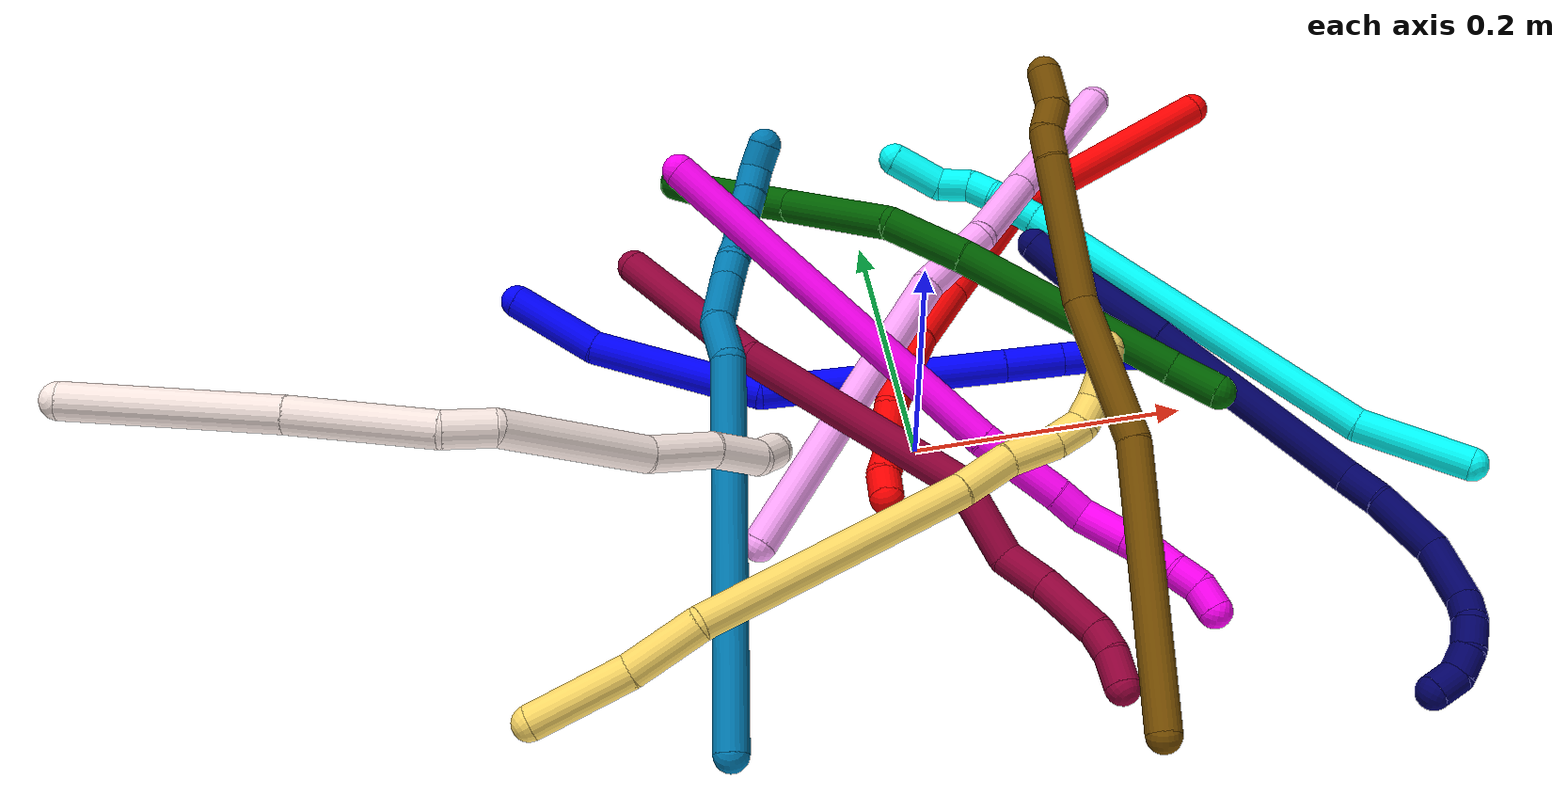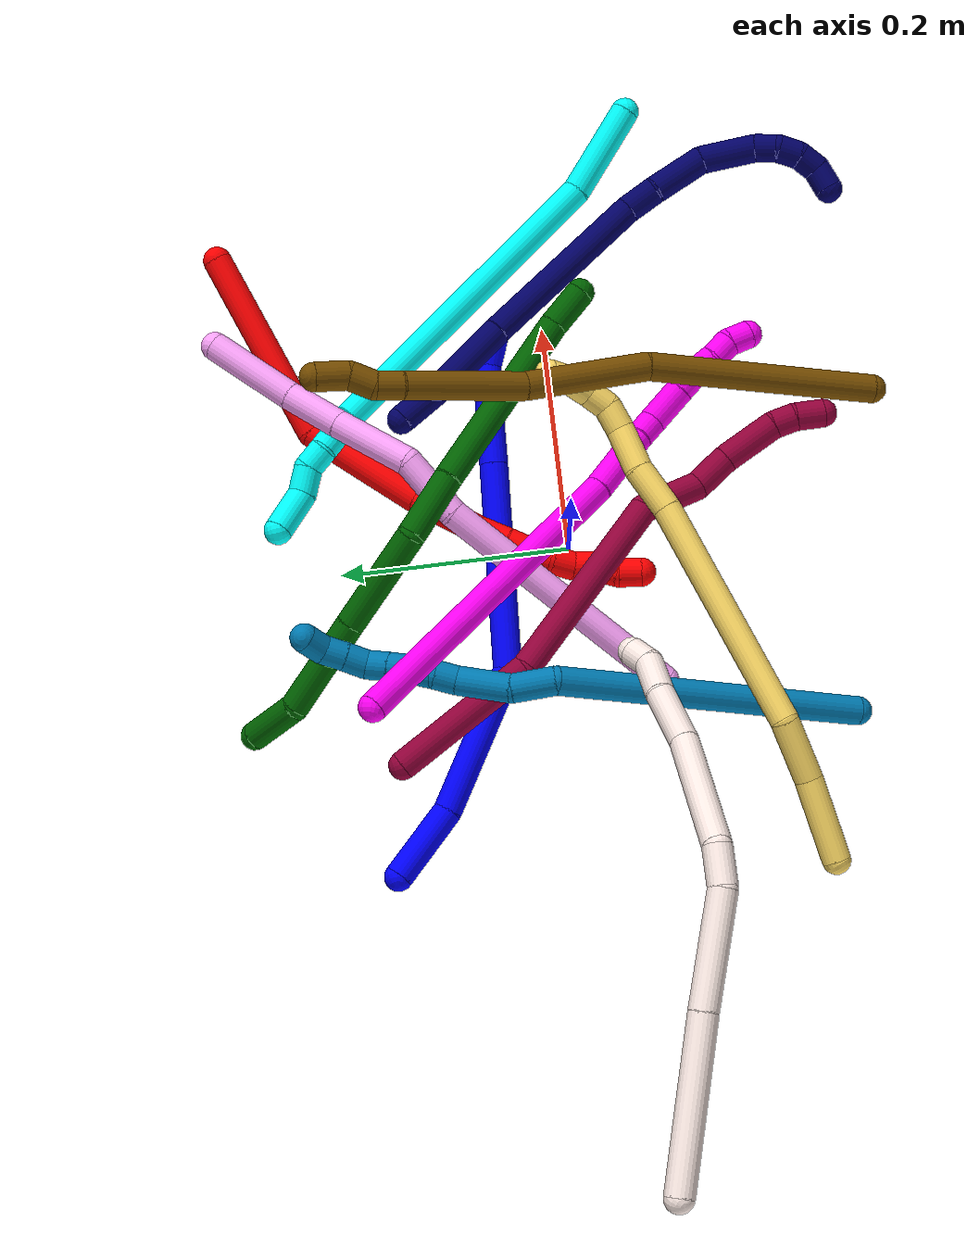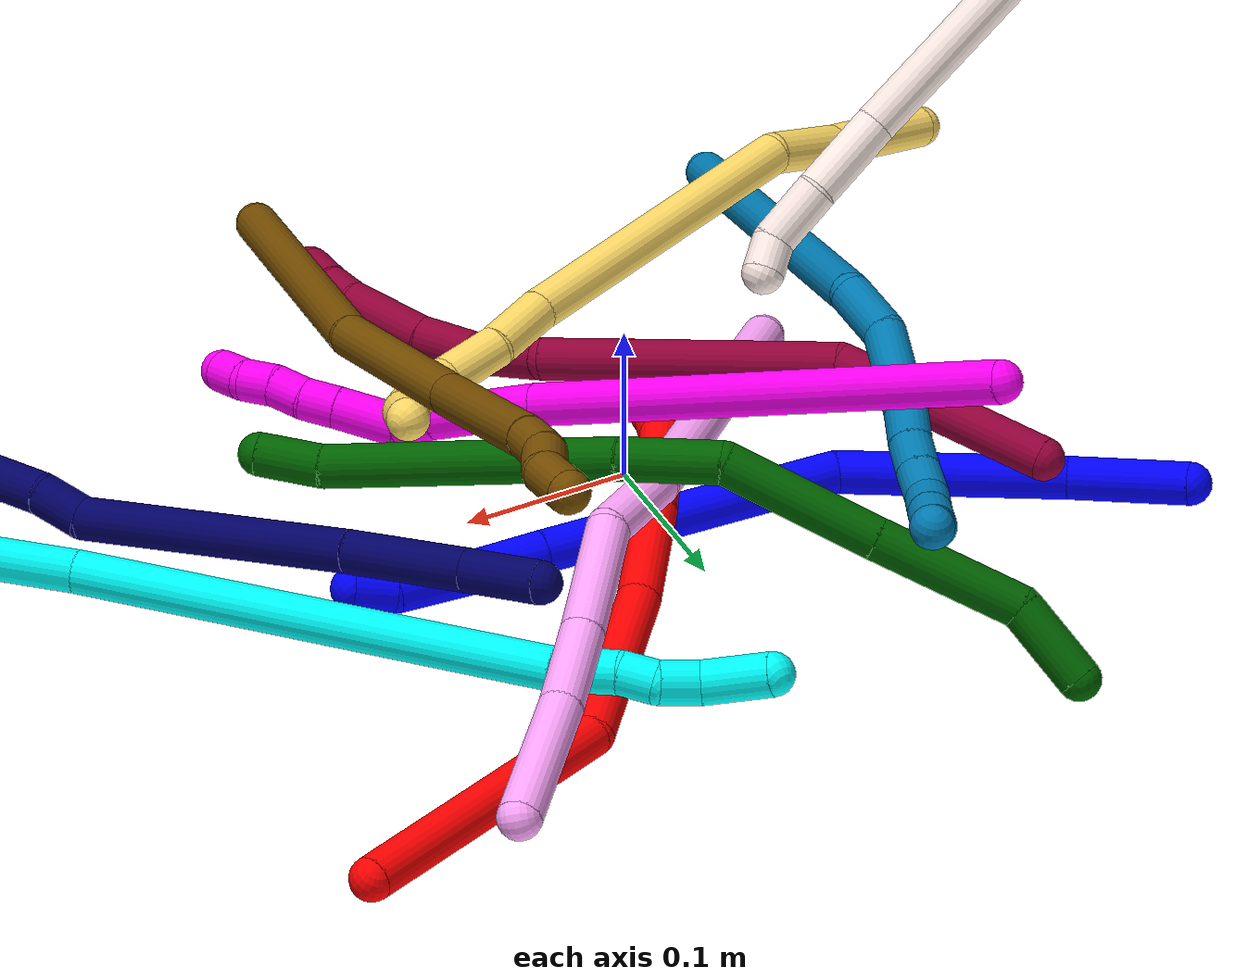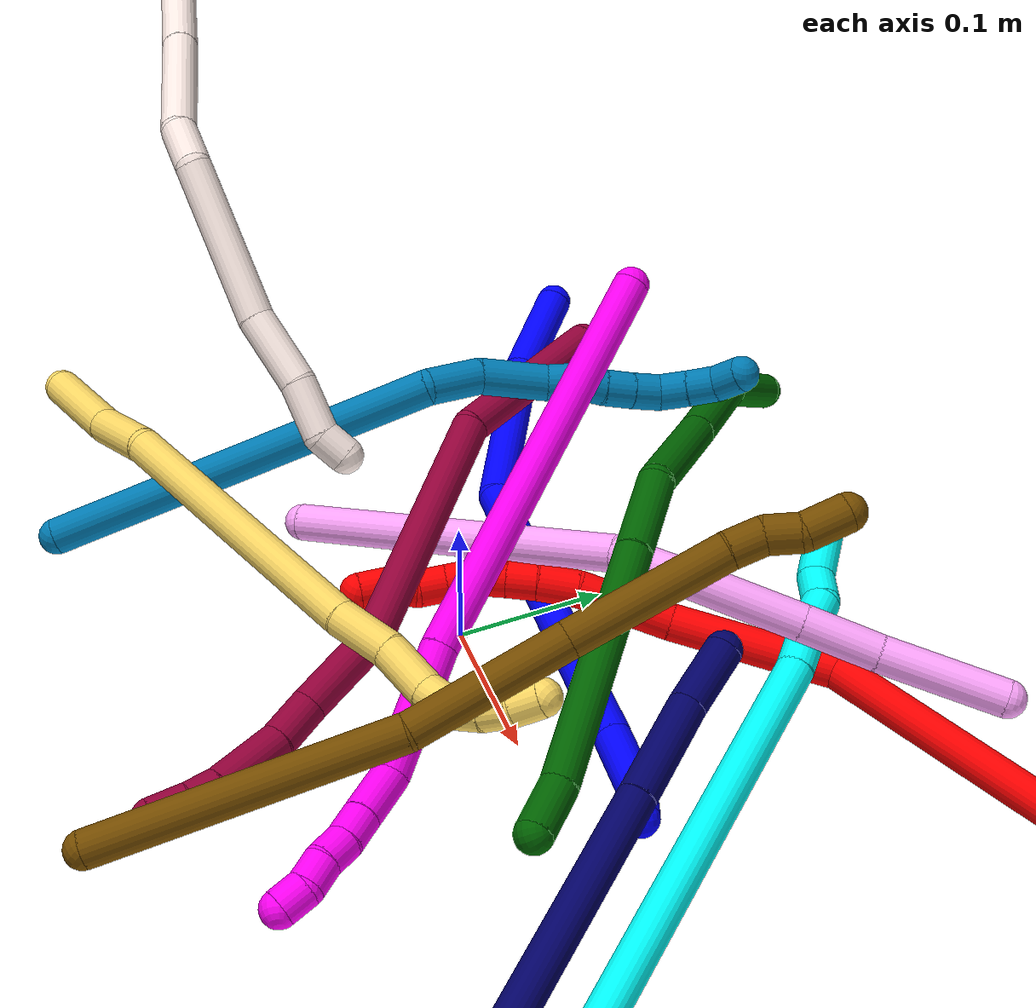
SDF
<sdf version="1.7">
 <world name="default">
  <plugin name="TubeGeneratorPlugin" filename="libtube_generator_plugin.so"/>
  <model name="photoneo_s_sensor">
   <static>1</static>
   <pose>0 0 2 1.57079 1.57079 3.14159</pose>
   <link name="link">
    <inertial><mass>0.1</mass></inertial>
    <sensor name="sensor" type="depth">
     <update_rate>30</update_rate>
     <camera>
      <horizontal_fov>1.22</horizontal_fov>
      <image><width>1920</width><height>1200</height><format>B8G8R8</format></image>
      <clip><near>0.1</near><far>4</far></clip>
      <depth_camera><output>points</output></depth_camera>
     </camera>
     <plugin name="camera_plugin" filename="libgazebo_ros_depth_camera.so">
      <baseline>0.2</baseline>
      <alwaysOn>1</alwaysOn>
      <updateRate>0.0</updateRate>
      <cameraName>camera_ir</cameraName>
      <imageTopicName>/camera/color/image_raw</imageTopicName>
      <cameraInfoTopicName>/camera/color/camera_info</cameraInfoTopicName>
      <depthImageTopicName>/camera/depth/image_raw</depthImageTopicName>
      <depthImageCameraInfoTopicName>/camera/depth/camera_info</depthImageCameraInfoTopicName>
      <pointCloudTopicName>/camera/depth/points</pointCloudTopicName>
      <frameName>fr_optical</frameName>
      <pointCloudCutoff>0.1</pointCloudCutoff>
      <pointCloudCutoffMax>2.0</pointCloudCutoffMax>
      <distortionK1>0</distortionK1>
      <distortionK2>0</distortionK2>
      <distortionK3>0</distortionK3>
      <distortionT1>0</distortionT1>
      <distortionT2>0</distortionT2>
      <CxPrime>0</CxPrime>
      <Cx>0</Cx>
      <Cy>0</Cy>
      <focalLength>0</focalLength>
      <hackBaseline>0</hackBaseline>
     </plugin>
    </sensor>
   </link>
  </model>
  <gravity>0 0 -9.8</gravity>
  <magnetic_field>6e-06 2.3e-05 -4.2e-05</magnetic_field>
  <atmosphere type="adiabatic"/>
  <physics name="default_physics" default="0" type="ode">
   <max_step_size>0.003</max_step_size>
   <real_time_factor>1</real_time_factor>
   <real_time_update_rate>1000</real_time_update_rate>
   <max_contacts>10000</max_contacts>
   <ode>
    <solver>
     <type>quick</type>
     <iters>100</iters>
     <sor>1.3</sor>
     <use_dynamic_moi_rescaling>0</use_dynamic_moi_rescaling>
    </solver>
    <constraints>
     <contact_max_correcting_vel>0</contact_max_correcting_vel>
     <contact_surface_layer>0.001</contact_surface_layer>
     <cfm>0</cfm>
     <erp>0.2</erp>
    </constraints>
   </ode>
  </physics>
  <scene><ambient>0.4 0.4 0.4 1</ambient><background>0.7 0.7 0.7 1</background><shadows>0</shadows></scene>
  <audio><device>default</device></audio>
  <spherical_coordinates>
   <surface_model>EARTH_WGS84</surface_model>
   <latitude_deg>0</latitude_deg>
   <longitude_deg>0</longitude_deg>
   <elevation>0</elevation>
   <heading_deg>0</heading_deg>
  </spherical_coordinates>
  <model name="bin">
   <static>1</static>
   <link name="bottom">
    <collision name="collision-bottom">
     <pose>0 0 -0.01 0 -0 0</pose>
     <geometry><box><size>0.8 0.6 0.02</size></box></geometry>
     <surface>
      <friction><ode><mu>100</mu><mu2>100</mu2></ode></friction>
      <contact><collide_bitmask>65535</collide_bitmask></contact>
     </surface>
    </collision>
   </link>
   <link name="west_wall">
    <collision name="collision-west_wall">
     <pose>-0.41 0 0.1 0 -0 0</pose>
     <geometry><box><size>0.02 0.6 0.2</size></box></geometry>
     <surface>
      <friction><ode><mu>100</mu><mu2>100</mu2></ode></friction>
      <contact><collide_bitmask>65535</collide_bitmask></contact>
     </surface>
    </collision>
   </link>
   <link name="east_wall">
    <collision name="collision-east_wall">
     <pose>0.41 0 0.1 0 -0 0</pose>
     <geometry><box><size>0.02 0.6 0.2</size></box></geometry>
     <surface>
      <friction><ode><mu>100</mu><mu2>100</mu2></ode></friction>
      <contact><collide_bitmask>65535</collide_bitmask></contact>
     </surface>
    </collision>
   </link>
   <link name="south_wall">
    <collision name="collision-south_wall">
     <pose>0 -0.31 0.1 0 -0 0</pose>
     <geometry><box><size>0.8 0.02 0.2</size></box></geometry>
     <surface>
      <friction><ode><mu>100</mu><mu2>100</mu2></ode></friction>
      <contact><collide_bitmask>65535</collide_bitmask></contact>
     </surface>
    </collision>
   </link>
   <link name="north_wall">
    <collision name="collision-north_wall">
     <pose>0 0.31 0.1 0 -0 0</pose>
     <geometry><box><size>0.8 0.02 0.2</size></box></geometry>
     <surface>
      <friction><ode><mu>100</mu><mu2>100</mu2></ode></friction>
      <contact><collide_bitmask>65535</collide_bitmask></contact>
     </surface>
    </collision>
   </link>
  </model>
  <model name="1">
   <static>0</static>
   <link name="1">
    <collision name="collision-cylinder-e_1_1_4">
     <pose>0.019555 0.013454 0.026318 -0.472562 0.584486 -0.144627</pose>
     <geometry><cylinder><radius>0.0125</radius><length>0.070882</length></cylinder></geometry>
     <surface>
      <friction><ode><mu>1.16</mu><mu2>1.16</mu2><slip1>0</slip1><slip2>0</slip2></ode></friction>
      <contact><ode><kp>1e+06</kp><kd>1</kd><max_vel>0</max_vel><min_depth>0.001</min_depth></ode></contact>
     </surface>
    </collision>
    <visual name="visual-cylinder-e_1_1_4">
     <pose>0.019555 0.013454 0.026318 -0.472562 0.584486 -0.144627</pose>
     <geometry><cylinder><radius>0.0125</radius><length>0.070882</length></cylinder></geometry>
     <material><ambient>0 0 1 1</ambient></material>
    </visual>
    <collision name="collision-cylinder-e_2_4_5">
     <pose>0.080134 0.035462 0.104098 -0.164734 0.666375 -0.057127</pose>
     <geometry><cylinder><radius>0.0125</radius><length>0.13273</length></cylinder></geometry>
     <surface>
      <friction><ode><mu>1.16</mu><mu2>1.16</mu2><slip1>0</slip1><slip2>0</slip2></ode></friction>
      <contact><ode><kp>1e+06</kp><kd>1</kd><max_vel>0</max_vel><min_depth>0.001</min_depth></ode></contact>
     </surface>
    </collision>
    <visual name="visual-cylinder-e_2_4_5">
     <pose>0.080134 0.035462 0.104098 -0.164734 0.666375 -0.057127</pose>
     <geometry><cylinder><radius>0.0125</radius><length>0.13273</length></cylinder></geometry>
     <material><ambient>0 0 1 1</ambient></material>
    </visual>
    <collision name="collision-cylinder-e_3_5_6">
     <pose>0.161346 0.017553 0.233184 0.328572 0.455655 0.076835</pose>
     <geometry><cylinder><radius>0.0125</radius><length>0.18266</length></cylinder></geometry>
     <surface>
      <friction><ode><mu>1.16</mu><mu2>1.16</mu2><slip1>0</slip1><slip2>0</slip2></ode></friction>
      <contact><ode><kp>1e+06</kp><kd>1</kd><max_vel>0</max_vel><min_depth>0.001</min_depth></ode></contact>
     </surface>
    </collision>
    <visual name="visual-cylinder-e_3_5_6">
     <pose>0.161346 0.017553 0.233184 0.328572 0.455655 0.076835</pose>
     <geometry><cylinder><radius>0.0125</radius><length>0.18266</length></cylinder></geometry>
     <material><ambient>0 0 1 1</ambient></material>
    </visual>
    <collision name="collision-cylinder-e_4_6_7">
     <pose>0.210836 -0.015401 0.329498 0.334169 0.439396 0.075287</pose>
     <geometry><cylinder><radius>0.0125</radius><length>0.043722</length></cylinder></geometry>
     <surface>
      <friction><ode><mu>1.16</mu><mu2>1.16</mu2><slip1>0</slip1><slip2>0</slip2></ode></friction>
      <contact><ode><kp>1e+06</kp><kd>1</kd><max_vel>0</max_vel><min_depth>0.001</min_depth></ode></contact>
     </surface>
    </collision>
    <visual name="visual-cylinder-e_4_6_7">
     <pose>0.210836 -0.015401 0.329498 0.334169 0.439396 0.075287</pose>
     <geometry><cylinder><radius>0.0125</radius><length>0.043722</length></cylinder></geometry>
     <material><ambient>0 0 1 1</ambient></material>
    </visual>
    <collision name="collision-cylinder-e_5_7_8">
     <pose>0.230597 -0.028307 0.36743 0.321922 0.476184 0.07877</pose>
     <geometry><cylinder><radius>0.0125</radius><length>0.045647</length></cylinder></geometry>
     <surface>
      <friction><ode><mu>1.16</mu><mu2>1.16</mu2><slip1>0</slip1><slip2>0</slip2></ode></friction>
      <contact><ode><kp>1e+06</kp><kd>1</kd><max_vel>0</max_vel><min_depth>0.001</min_depth></ode></contact>
     </surface>
    </collision>
    <visual name="visual-cylinder-e_5_7_8">
     <pose>0.230597 -0.028307 0.36743 0.321922 0.476184 0.07877</pose>
     <geometry><cylinder><radius>0.0125</radius><length>0.045647</length></cylinder></geometry>
     <material><ambient>0 0 1 1</ambient></material>
    </visual>
    <collision name="collision-cylinder-e_6_8_2">
     <pose>0.249553 -0.035866 0.395327 0.131086 0.771734 0.053315</pose>
     <geometry><cylinder><radius>0.0125</radius><length>0.024359</length></cylinder></geometry>
     <surface>
      <friction><ode><mu>1.16</mu><mu2>1.16</mu2><slip1>0</slip1><slip2>0</slip2></ode></friction>
      <contact><ode><kp>1e+06</kp><kd>1</kd><max_vel>0</max_vel><min_depth>0.001</min_depth></ode></contact>
     </surface>
    </collision>
    <visual name="visual-cylinder-e_6_8_2">
     <pose>0.249553 -0.035866 0.395327 0.131086 0.771734 0.053315</pose>
     <geometry><cylinder><radius>0.0125</radius><length>0.024359</length></cylinder></geometry>
     <material><ambient>0 0 1 1</ambient></material>
    </visual>
    <collision name="collision-sphere-2">
     <pose>0.258047 -0.037007 0.403981 0 -0 0</pose>
     <geometry><sphere><radius>0.0125</radius></sphere></geometry>
     <surface>
      <friction><ode><mu>1.16</mu><mu2>1.16</mu2><slip1>0</slip1><slip2>0</slip2></ode></friction>
      <contact><ode><kp>1e+06</kp><kd>1</kd><max_vel>0</max_vel><min_depth>0.001</min_depth></ode></contact>
     </surface>
    </collision>
    <visual name="visual-sphere-2">
     <pose>0.258047 -0.037007 0.403981 0 -0 0</pose>
     <geometry><sphere><radius>0.0125</radius></sphere></geometry>
     <material><ambient>0 0 1 1</ambient></material>
    </visual>
    <collision name="collision-sphere-4">
     <pose>0.039111 0.026907 0.052637 0 -0 0</pose>
     <geometry><sphere><radius>0.0125</radius></sphere></geometry>
     <surface>
      <friction><ode><mu>1.16</mu><mu2>1.16</mu2><slip1>0</slip1><slip2>0</slip2></ode></friction>
      <contact><ode><kp>1e+06</kp><kd>1</kd><max_vel>0</max_vel><min_depth>0.001</min_depth></ode></contact>
     </surface>
    </collision>
    <visual name="visual-sphere-4">
     <pose>0.039111 0.026907 0.052637 0 -0 0</pose>
     <geometry><sphere><radius>0.0125</radius></sphere></geometry>
     <material><ambient>0 0 1 1</ambient></material>
    </visual>
    <collision name="collision-sphere-1">
     <geometry><sphere><radius>0.0125</radius></sphere></geometry>
     <surface>
      <friction><ode><mu>1.16</mu><mu2>1.16</mu2><slip1>0</slip1><slip2>0</slip2></ode></friction>
      <contact><ode><kp>1e+06</kp><kd>1</kd><max_vel>0</max_vel><min_depth>0.001</min_depth></ode></contact>
     </surface>
    </collision>
    <visual name="visual-sphere-1">
     <geometry><sphere><radius>0.0125</radius></sphere></geometry>
     <material><ambient>0 0 1 1</ambient></material>
    </visual>
    <collision name="collision-sphere-8">
     <pose>0.241059 -0.034725 0.386672 0 -0 0</pose>
     <geometry><sphere><radius>0.0125</radius></sphere></geometry>
     <surface>
      <friction><ode><mu>1.16</mu><mu2>1.16</mu2><slip1>0</slip1><slip2>0</slip2></ode></friction>
      <contact><ode><kp>1e+06</kp><kd>1</kd><max_vel>0</max_vel><min_depth>0.001</min_depth></ode></contact>
     </surface>
    </collision>
    <visual name="visual-sphere-8">
     <pose>0.241059 -0.034725 0.386672 0 -0 0</pose>
     <geometry><sphere><radius>0.0125</radius></sphere></geometry>
     <material><ambient>0 0 1 1</ambient></material>
    </visual>
    <collision name="collision-sphere-5">
     <pose>0.121157 0.044017 0.155559 0 -0 0</pose>
     <geometry><sphere><radius>0.0125</radius></sphere></geometry>
     <surface>
      <friction><ode><mu>1.16</mu><mu2>1.16</mu2><slip1>0</slip1><slip2>0</slip2></ode></friction>
      <contact><ode><kp>1e+06</kp><kd>1</kd><max_vel>0</max_vel><min_depth>0.001</min_depth></ode></contact>
     </surface>
    </collision>
    <visual name="visual-sphere-5">
     <pose>0.121157 0.044017 0.155559 0 -0 0</pose>
     <geometry><sphere><radius>0.0125</radius></sphere></geometry>
     <material><ambient>0 0 1 1</ambient></material>
    </visual>
    <collision name="collision-sphere-6">
     <pose>0.201536 -0.008912 0.310808 0 -0 0</pose>
     <geometry><sphere><radius>0.0125</radius></sphere></geometry>
     <surface>
      <friction><ode><mu>1.16</mu><mu2>1.16</mu2><slip1>0</slip1><slip2>0</slip2></ode></friction>
      <contact><ode><kp>1e+06</kp><kd>1</kd><max_vel>0</max_vel><min_depth>0.001</min_depth></ode></contact>
     </surface>
    </collision>
    <visual name="visual-sphere-6">
     <pose>0.201536 -0.008912 0.310808 0 -0 0</pose>
     <geometry><sphere><radius>0.0125</radius></sphere></geometry>
     <material><ambient>0 0 1 1</ambient></material>
    </visual>
    <collision name="collision-sphere-7">
     <pose>0.220135 -0.021889 0.348188 0 -0 0</pose>
     <geometry><sphere><radius>0.0125</radius></sphere></geometry>
     <surface>
      <friction><ode><mu>1.16</mu><mu2>1.16</mu2><slip1>0</slip1><slip2>0</slip2></ode></friction>
      <contact><ode><kp>1e+06</kp><kd>1</kd><max_vel>0</max_vel><min_depth>0.001</min_depth></ode></contact>
     </surface>
    </collision>
    <visual name="visual-sphere-7">
     <pose>0.220135 -0.021889 0.348188 0 -0 0</pose>
     <geometry><sphere><radius>0.0125</radius></sphere></geometry>
     <material><ambient>0 0 1 1</ambient></material>
    </visual>
    <inertial>
     <pose>0.134634 0.012055 0.198168 0 -0 0</pose>
     <mass>0.5</mass>
     <inertia>
      <ixx>0.000707</ixx>
      <ixy>0</ixy>
      <ixz>0</ixz>
      <iyy>0.00076</iyy>
      <iyz>0</iyz>
      <izz>-0.00023</izz>
     </inertia>
    </inertial>
   </link>
   <pose>-0.26911 0.17903 0.022063 -2.46077 -0.831567 -0.915773</pose>
  </model>
  <model name="2">
   <static>0</static>
   <link name="2">
    <collision name="collision-cylinder-e_1_1_4">
     <pose>-0.068611 -0.054743 -0.003369 1.63226 -0.896426 -0.945379</pose>
     <geometry><cylinder><radius>0.0125</radius><length>0.175677</length></cylinder></geometry>
     <surface>
      <friction><ode><mu>1.16</mu><mu2>1.16</mu2><slip1>0</slip1><slip2>0</slip2></ode></friction>
      <contact><ode><kp>1e+06</kp><kd>1</kd><max_vel>0</max_vel><min_depth>0.001</min_depth></ode></contact>
     </surface>
    </collision>
    <visual name="visual-cylinder-e_1_1_4">
     <pose>-0.068611 -0.054743 -0.003369 1.63226 -0.896426 -0.945379</pose>
     <geometry><cylinder><radius>0.0125</radius><length>0.175677</length></cylinder></geometry>
     <material><ambient>1 0 0 1</ambient></material>
    </visual>
    <collision name="collision-cylinder-e_2_4_5">
     <pose>-0.158931 -0.160828 -0.012524 1.68302 -0.39779 -0.443677</pose>
     <geometry><cylinder><radius>0.0125</radius><length>0.112085</length></cylinder></geometry>
     <surface>
      <friction><ode><mu>1.16</mu><mu2>1.16</mu2><slip1>0</slip1><slip2>0</slip2></ode></friction>
      <contact><ode><kp>1e+06</kp><kd>1</kd><max_vel>0</max_vel><min_depth>0.001</min_depth></ode></contact>
     </surface>
    </collision>
    <visual name="visual-cylinder-e_2_4_5">
     <pose>-0.158931 -0.160828 -0.012524 1.68302 -0.39779 -0.443677</pose>
     <geometry><cylinder><radius>0.0125</radius><length>0.112085</length></cylinder></geometry>
     <material><ambient>1 0 0 1</ambient></material>
    </visual>
    <collision name="collision-cylinder-e_3_5_6">
     <pose>-0.189025 -0.243135 -0.017149 1.53334 -0.264241 -0.254631</pose>
     <geometry><cylinder><radius>0.0125</radius><length>0.064202</length></cylinder></geometry>
     <surface>
      <friction><ode><mu>1.16</mu><mu2>1.16</mu2><slip1>0</slip1><slip2>0</slip2></ode></friction>
      <contact><ode><kp>1e+06</kp><kd>1</kd><max_vel>0</max_vel><min_depth>0.001</min_depth></ode></contact>
     </surface>
    </collision>
    <visual name="visual-cylinder-e_3_5_6">
     <pose>-0.189025 -0.243135 -0.017149 1.53334 -0.264241 -0.254631</pose>
     <geometry><cylinder><radius>0.0125</radius><length>0.064202</length></cylinder></geometry>
     <material><ambient>1 0 0 1</ambient></material>
    </visual>
    <collision name="collision-cylinder-e_4_6_7">
     <pose>-0.200538 -0.287116 -0.018028 1.72622 -0.2332 -0.272135</pose>
     <geometry><cylinder><radius>0.0125</radius><length>0.027082</length></cylinder></geometry>
     <surface>
      <friction><ode><mu>1.16</mu><mu2>1.16</mu2><slip1>0</slip1><slip2>0</slip2></ode></friction>
      <contact><ode><kp>1e+06</kp><kd>1</kd><max_vel>0</max_vel><min_depth>0.001</min_depth></ode></contact>
     </surface>
    </collision>
    <visual name="visual-cylinder-e_4_6_7">
     <pose>-0.200538 -0.287116 -0.018028 1.72622 -0.2332 -0.272135</pose>
     <geometry><cylinder><radius>0.0125</radius><length>0.027082</length></cylinder></geometry>
     <material><ambient>1 0 0 1</ambient></material>
    </visual>
    <collision name="collision-cylinder-e_5_7_8">
     <pose>-0.206321 -0.309823 -0.022481 1.81484 -0.259647 -0.331051</pose>
     <geometry><cylinder><radius>0.0125</radius><length>0.020668</length></cylinder></geometry>
     <surface>
      <friction><ode><mu>1.16</mu><mu2>1.16</mu2><slip1>0</slip1><slip2>0</slip2></ode></friction>
      <contact><ode><kp>1e+06</kp><kd>1</kd><max_vel>0</max_vel><min_depth>0.001</min_depth></ode></contact>
     </surface>
    </collision>
    <visual name="visual-cylinder-e_5_7_8">
     <pose>-0.206321 -0.309823 -0.022481 1.81484 -0.259647 -0.331051</pose>
     <geometry><cylinder><radius>0.0125</radius><length>0.020668</length></cylinder></geometry>
     <material><ambient>1 0 0 1</ambient></material>
    </visual>
    <collision name="collision-cylinder-e_6_8_9">
     <pose>-0.211244 -0.329024 -0.027361 1.82463 -0.227109 -0.292707</pose>
     <geometry><cylinder><radius>0.0125</radius><length>0.020166</length></cylinder></geometry>
     <surface>
      <friction><ode><mu>1.16</mu><mu2>1.16</mu2><slip1>0</slip1><slip2>0</slip2></ode></friction>
      <contact><ode><kp>1e+06</kp><kd>1</kd><max_vel>0</max_vel><min_depth>0.001</min_depth></ode></contact>
     </surface>
    </collision>
    <visual name="visual-cylinder-e_6_8_9">
     <pose>-0.211244 -0.329024 -0.027361 1.82463 -0.227109 -0.292707</pose>
     <geometry><cylinder><radius>0.0125</radius><length>0.020166</length></cylinder></geometry>
     <material><ambient>1 0 0 1</ambient></material>
    </visual>
    <collision name="collision-cylinder-e_7_9_10">
     <pose>-0.214813 -0.347104 -0.034895 2.10474 -0.129682 -0.226668</pose>
     <geometry><cylinder><radius>0.0125</radius><length>0.020082</length></cylinder></geometry>
     <surface>
      <friction><ode><mu>1.16</mu><mu2>1.16</mu2><slip1>0</slip1><slip2>0</slip2></ode></friction>
      <contact><ode><kp>1e+06</kp><kd>1</kd><max_vel>0</max_vel><min_depth>0.001</min_depth></ode></contact>
     </surface>
    </collision>
    <visual name="visual-cylinder-e_7_9_10">
     <pose>-0.214813 -0.347104 -0.034895 2.10474 -0.129682 -0.226668</pose>
     <geometry><cylinder><radius>0.0125</radius><length>0.020082</length></cylinder></geometry>
     <material><ambient>1 0 0 1</ambient></material>
    </visual>
    <collision name="collision-cylinder-e_8_10_11">
     <pose>-0.214812 -0.364962 -0.043444 1.92944 0.130285 0.187689</pose>
     <geometry><cylinder><radius>0.0125</radius><length>0.020005</length></cylinder></geometry>
     <surface>
      <friction><ode><mu>1.16</mu><mu2>1.16</mu2><slip1>0</slip1><slip2>0</slip2></ode></friction>
      <contact><ode><kp>1e+06</kp><kd>1</kd><max_vel>0</max_vel><min_depth>0.001</min_depth></ode></contact>
     </surface>
    </collision>
    <visual name="visual-cylinder-e_8_10_11">
     <pose>-0.214812 -0.364962 -0.043444 1.92944 0.130285 0.187689</pose>
     <geometry><cylinder><radius>0.0125</radius><length>0.020005</length></cylinder></geometry>
     <material><ambient>1 0 0 1</ambient></material>
    </visual>
    <collision name="collision-cylinder-e_9_11_12">
     <pose>-0.214966 -0.384011 -0.048605 1.74116 -0.145657 -0.172729</pose>
     <geometry><cylinder><radius>0.0125</radius><length>0.020024</length></cylinder></geometry>
     <surface>
      <friction><ode><mu>1.16</mu><mu2>1.16</mu2><slip1>0</slip1><slip2>0</slip2></ode></friction>
      <contact><ode><kp>1e+06</kp><kd>1</kd><max_vel>0</max_vel><min_depth>0.001</min_depth></ode></contact>
     </surface>
    </collision>
    <visual name="visual-cylinder-e_9_11_12">
     <pose>-0.214966 -0.384011 -0.048605 1.74116 -0.145657 -0.172729</pose>
     <geometry><cylinder><radius>0.0125</radius><length>0.020024</length></cylinder></geometry>
     <material><ambient>1 0 0 1</ambient></material>
    </visual>
    <collision name="collision-cylinder-e_10_12_2">
     <pose>-0.21459 -0.403054 -0.053543 1.90857 0.183802 0.258647</pose>
     <geometry><cylinder><radius>0.0125</radius><length>0.020009</length></cylinder></geometry>
     <surface>
      <friction><ode><mu>1.16</mu><mu2>1.16</mu2><slip1>0</slip1><slip2>0</slip2></ode></friction>
      <contact><ode><kp>1e+06</kp><kd>1</kd><max_vel>0</max_vel><min_depth>0.001</min_depth></ode></contact>
     </surface>
    </collision>
    <visual name="visual-cylinder-e_10_12_2">
     <pose>-0.21459 -0.403054 -0.053543 1.90857 0.183802 0.258647</pose>
     <geometry><cylinder><radius>0.0125</radius><length>0.020009</length></cylinder></geometry>
     <material><ambient>1 0 0 1</ambient></material>
    </visual>
    <collision name="collision-sphere-2">
     <pose>-0.212762 -0.412334 -0.056803 0 -0 0</pose>
     <geometry><sphere><radius>0.0125</radius></sphere></geometry>
     <surface>
      <friction><ode><mu>1.16</mu><mu2>1.16</mu2><slip1>0</slip1><slip2>0</slip2></ode></friction>
      <contact><ode><kp>1e+06</kp><kd>1</kd><max_vel>0</max_vel><min_depth>0.001</min_depth></ode></contact>
     </surface>
    </collision>
    <visual name="visual-sphere-2">
     <pose>-0.212762 -0.412334 -0.056803 0 -0 0</pose>
     <geometry><sphere><radius>0.0125</radius></sphere></geometry>
     <material><ambient>1 0 0 1</ambient></material>
    </visual>
    <collision name="collision-sphere-12">
     <pose>-0.216419 -0.393773 -0.050284 0 -0 0</pose>
     <geometry><sphere><radius>0.0125</radius></sphere></geometry>
     <surface>
      <friction><ode><mu>1.16</mu><mu2>1.16</mu2><slip1>0</slip1><slip2>0</slip2></ode></friction>
      <contact><ode><kp>1e+06</kp><kd>1</kd><max_vel>0</max_vel><min_depth>0.001</min_depth></ode></contact>
     </surface>
    </collision>
    <visual name="visual-sphere-12">
     <pose>-0.216419 -0.393773 -0.050284 0 -0 0</pose>
     <geometry><sphere><radius>0.0125</radius></sphere></geometry>
     <material><ambient>1 0 0 1</ambient></material>
    </visual>
    <collision name="collision-sphere-11">
     <pose>-0.213513 -0.374248 -0.046925 0 -0 0</pose>
     <geometry><sphere><radius>0.0125</radius></sphere></geometry>
     <surface>
      <friction><ode><mu>1.16</mu><mu2>1.16</mu2><slip1>0</slip1><slip2>0</slip2></ode></friction>
      <contact><ode><kp>1e+06</kp><kd>1</kd><max_vel>0</max_vel><min_depth>0.001</min_depth></ode></contact>
     </surface>
    </collision>
    <visual name="visual-sphere-11">
     <pose>-0.213513 -0.374248 -0.046925 0 -0 0</pose>
     <geometry><sphere><radius>0.0125</radius></sphere></geometry>
     <material><ambient>1 0 0 1</ambient></material>
    </visual>
    <collision name="collision-sphere-10">
     <pose>-0.216112 -0.355675 -0.039963 0 -0 0</pose>
     <geometry><sphere><radius>0.0125</radius></sphere></geometry>
     <surface>
      <friction><ode><mu>1.16</mu><mu2>1.16</mu2><slip1>0</slip1><slip2>0</slip2></ode></friction>
      <contact><ode><kp>1e+06</kp><kd>1</kd><max_vel>0</max_vel><min_depth>0.001</min_depth></ode></contact>
     </surface>
    </collision>
    <visual name="visual-sphere-10">
     <pose>-0.216112 -0.355675 -0.039963 0 -0 0</pose>
     <geometry><sphere><radius>0.0125</radius></sphere></geometry>
     <material><ambient>1 0 0 1</ambient></material>
    </visual>
    <collision name="collision-sphere-9">
     <pose>-0.213515 -0.338534 -0.029828 0 -0 0</pose>
     <geometry><sphere><radius>0.0125</radius></sphere></geometry>
     <surface>
      <friction><ode><mu>1.16</mu><mu2>1.16</mu2><slip1>0</slip1><slip2>0</slip2></ode></friction>
      <contact><ode><kp>1e+06</kp><kd>1</kd><max_vel>0</max_vel><min_depth>0.001</min_depth></ode></contact>
     </surface>
    </collision>
    <visual name="visual-sphere-9">
     <pose>-0.213515 -0.338534 -0.029828 0 -0 0</pose>
     <geometry><sphere><radius>0.0125</radius></sphere></geometry>
     <material><ambient>1 0 0 1</ambient></material>
    </visual>
    <collision name="collision-sphere-4">
     <pose>-0.137221 -0.109486 -0.006738 0 -0 0</pose>
     <geometry><sphere><radius>0.0125</radius></sphere></geometry>
     <surface>
      <friction><ode><mu>1.16</mu><mu2>1.16</mu2><slip1>0</slip1><slip2>0</slip2></ode></friction>
      <contact><ode><kp>1e+06</kp><kd>1</kd><max_vel>0</max_vel><min_depth>0.001</min_depth></ode></contact>
     </surface>
    </collision>
    <visual name="visual-sphere-4">
     <pose>-0.137221 -0.109486 -0.006738 0 -0 0</pose>
     <geometry><sphere><radius>0.0125</radius></sphere></geometry>
     <material><ambient>1 0 0 1</ambient></material>
    </visual>
    <collision name="collision-sphere-1">
     <geometry><sphere><radius>0.0125</radius></sphere></geometry>
     <surface>
      <friction><ode><mu>1.16</mu><mu2>1.16</mu2><slip1>0</slip1><slip2>0</slip2></ode></friction>
      <contact><ode><kp>1e+06</kp><kd>1</kd><max_vel>0</max_vel><min_depth>0.001</min_depth></ode></contact>
     </surface>
    </collision>
    <visual name="visual-sphere-1">
     <geometry><sphere><radius>0.0125</radius></sphere></geometry>
     <material><ambient>1 0 0 1</ambient></material>
    </visual>
    <collision name="collision-sphere-8">
     <pose>-0.208974 -0.319515 -0.024894 0 -0 0</pose>
     <geometry><sphere><radius>0.0125</radius></sphere></geometry>
     <surface>
      <friction><ode><mu>1.16</mu><mu2>1.16</mu2><slip1>0</slip1><slip2>0</slip2></ode></friction>
      <contact><ode><kp>1e+06</kp><kd>1</kd><max_vel>0</max_vel><min_depth>0.001</min_depth></ode></contact>
     </surface>
    </collision>
    <visual name="visual-sphere-8">
     <pose>-0.208974 -0.319515 -0.024894 0 -0 0</pose>
     <geometry><sphere><radius>0.0125</radius></sphere></geometry>
     <material><ambient>1 0 0 1</ambient></material>
    </visual>
    <collision name="collision-sphere-5">
     <pose>-0.180641 -0.21217 -0.01831 0 -0 0</pose>
     <geometry><sphere><radius>0.0125</radius></sphere></geometry>
     <surface>
      <friction><ode><mu>1.16</mu><mu2>1.16</mu2><slip1>0</slip1><slip2>0</slip2></ode></friction>
      <contact><ode><kp>1e+06</kp><kd>1</kd><max_vel>0</max_vel><min_depth>0.001</min_depth></ode></contact>
     </surface>
    </collision>
    <visual name="visual-sphere-5">
     <pose>-0.180641 -0.21217 -0.01831 0 -0 0</pose>
     <geometry><sphere><radius>0.0125</radius></sphere></geometry>
     <material><ambient>1 0 0 1</ambient></material>
    </visual>
    <collision name="collision-sphere-6">
     <pose>-0.197409 -0.2741 -0.015989 0 -0 0</pose>
     <geometry><sphere><radius>0.0125</radius></sphere></geometry>
     <surface>
      <friction><ode><mu>1.16</mu><mu2>1.16</mu2><slip1>0</slip1><slip2>0</slip2></ode></friction>
      <contact><ode><kp>1e+06</kp><kd>1</kd><max_vel>0</max_vel><min_depth>0.001</min_depth></ode></contact>
     </surface>
    </collision>
    <visual name="visual-sphere-6">
     <pose>-0.197409 -0.2741 -0.015989 0 -0 0</pose>
     <geometry><sphere><radius>0.0125</radius></sphere></geometry>
     <material><ambient>1 0 0 1</ambient></material>
    </visual>
    <collision name="collision-sphere-7">
     <pose>-0.203668 -0.300131 -0.020068 0 -0 0</pose>
     <geometry><sphere><radius>0.0125</radius></sphere></geometry>
     <surface>
      <friction><ode><mu>1.16</mu><mu2>1.16</mu2><slip1>0</slip1><slip2>0</slip2></ode></friction>
      <contact><ode><kp>1e+06</kp><kd>1</kd><max_vel>0</max_vel><min_depth>0.001</min_depth></ode></contact>
     </surface>
    </collision>
    <visual name="visual-sphere-7">
     <pose>-0.203668 -0.300131 -0.020068 0 -0 0</pose>
     <geometry><sphere><radius>0.0125</radius></sphere></geometry>
     <material><ambient>1 0 0 1</ambient></material>
    </visual>
    <inertial>
     <pose>-0.146335 -0.188186 -0.016431 0 -0 0</pose>
     <mass>0.5</mass>
     <inertia><ixx>-2e-06</ixx><ixy>0</ixy><ixz>0</ixz><iyy>-3.9e-05</iyy><iyz>0</iyz><izz>0.000841</izz></inertia>
    </inertial>
   </link>
   <pose>0.29064 0.27745 0.024914 -0.299995 -0.275425 -0.270124</pose>
  </model>
  <model name="3">
   <static>0</static>
   <link name="3">
    <collision name="collision-cylinder-e_1_1_4">
     <pose>-0.028175 0.011627 -0.029843 -2.77008 -0.721492 2.2173</pose>
     <geometry><cylinder><radius>0.0125</radius><length>0.085314</length></cylinder></geometry>
     <surface>
      <friction><ode><mu>1.16</mu><mu2>1.16</mu2><slip1>0</slip1><slip2>0</slip2></ode></friction>
      <contact><ode><kp>1e+06</kp><kd>1</kd><max_vel>0</max_vel><min_depth>0.001</min_depth></ode></contact>
     </surface>
    </collision>
    <visual name="visual-cylinder-e_1_1_4">
     <pose>-0.028175 0.011627 -0.029843 -2.77008 -0.721492 2.2173</pose>
     <geometry><cylinder><radius>0.0125</radius><length>0.085314</length></cylinder></geometry>
     <material><ambient>0.003922 1 0.996078 1</ambient></material>
    </visual>
    <collision name="collision-cylinder-e_2_4_5">
     <pose>-0.123216 0.072585 -0.179647 -2.75144 -0.475977 1.77455</pose>
     <geometry><cylinder><radius>0.0125</radius><length>0.291859</length></cylinder></geometry>
     <surface>
      <friction><ode><mu>1.16</mu><mu2>1.16</mu2><slip1>0</slip1><slip2>0</slip2></ode></friction>
      <contact><ode><kp>1e+06</kp><kd>1</kd><max_vel>0</max_vel><min_depth>0.001</min_depth></ode></contact>
     </surface>
    </collision>
    <visual name="visual-cylinder-e_2_4_5">
     <pose>-0.123216 0.072585 -0.179647 -2.75144 -0.475977 1.77455</pose>
     <geometry><cylinder><radius>0.0125</radius><length>0.291859</length></cylinder></geometry>
     <material><ambient>0.003922 1 0.996078 1</ambient></material>
    </visual>
    <collision name="collision-cylinder-e_3_5_6">
     <pose>-0.199999 0.130059 -0.313245 -2.6033 -0.558173 1.60894</pose>
     <geometry><cylinder><radius>0.0125</radius><length>0.037448</length></cylinder></geometry>
     <surface>
      <friction><ode><mu>1.16</mu><mu2>1.16</mu2><slip1>0</slip1><slip2>0</slip2></ode></friction>
      <contact><ode><kp>1e+06</kp><kd>1</kd><max_vel>0</max_vel><min_depth>0.001</min_depth></ode></contact>
     </surface>
    </collision>
    <visual name="visual-cylinder-e_3_5_6">
     <pose>-0.199999 0.130059 -0.313245 -2.6033 -0.558173 1.60894</pose>
     <geometry><cylinder><radius>0.0125</radius><length>0.037448</length></cylinder></geometry>
     <material><ambient>0.003922 1 0.996078 1</ambient></material>
    </visual>
    <collision name="collision-cylinder-e_4_6_7">
     <pose>-0.215729 0.1405 -0.335103 -2.86888 -0.597769 2.30369</pose>
     <geometry><cylinder><radius>0.0125</radius><length>0.020657</length></cylinder></geometry>
     <surface>
      <friction><ode><mu>1.16</mu><mu2>1.16</mu2><slip1>0</slip1><slip2>0</slip2></ode></friction>
      <contact><ode><kp>1e+06</kp><kd>1</kd><max_vel>0</max_vel><min_depth>0.001</min_depth></ode></contact>
     </surface>
    </collision>
    <visual name="visual-cylinder-e_4_6_7">
     <pose>-0.215729 0.1405 -0.335103 -2.86888 -0.597769 2.30369</pose>
     <geometry><cylinder><radius>0.0125</radius><length>0.020657</length></cylinder></geometry>
     <material><ambient>0.003922 1 0.996078 1</ambient></material>
    </visual>
    <collision name="collision-cylinder-e_5_7_8">
     <pose>-0.231936 0.146064 -0.348804 -2.60436 -1.02047 2.22739</pose>
     <geometry><cylinder><radius>0.0125</radius><length>0.024391</length></cylinder></geometry>
     <surface>
      <friction><ode><mu>1.16</mu><mu2>1.16</mu2><slip1>0</slip1><slip2>0</slip2></ode></friction>
      <contact><ode><kp>1e+06</kp><kd>1</kd><max_vel>0</max_vel><min_depth>0.001</min_depth></ode></contact>
     </surface>
    </collision>
    <visual name="visual-cylinder-e_5_7_8">
     <pose>-0.231936 0.146064 -0.348804 -2.60436 -1.02047 2.22739</pose>
     <geometry><cylinder><radius>0.0125</radius><length>0.024391</length></cylinder></geometry>
     <material><ambient>0.003922 1 0.996078 1</ambient></material>
    </visual>
    <collision name="collision-cylinder-e_6_8_2">
     <pose>-0.25313 0.160718 -0.366944 -2.40897 -0.565102 1.29564</pose>
     <geometry><cylinder><radius>0.0125</radius><length>0.040331</length></cylinder></geometry>
     <surface>
      <friction><ode><mu>1.16</mu><mu2>1.16</mu2><slip1>0</slip1><slip2>0</slip2></ode></friction>
      <contact><ode><kp>1e+06</kp><kd>1</kd><max_vel>0</max_vel><min_depth>0.001</min_depth></ode></contact>
     </surface>
    </collision>
    <visual name="visual-cylinder-e_6_8_2">
     <pose>-0.25313 0.160718 -0.366944 -2.40897 -0.565102 1.29564</pose>
     <geometry><cylinder><radius>0.0125</radius><length>0.040331</length></cylinder></geometry>
     <material><ambient>0.003922 1 0.996078 1</ambient></material>
    </visual>
    <collision name="collision-sphere-2">
     <pose>-0.263929 0.172109 -0.379605 0 -0 0</pose>
     <geometry><sphere><radius>0.0125</radius></sphere></geometry>
     <surface>
      <friction><ode><mu>1.16</mu><mu2>1.16</mu2><slip1>0</slip1><slip2>0</slip2></ode></friction>
      <contact><ode><kp>1e+06</kp><kd>1</kd><max_vel>0</max_vel><min_depth>0.001</min_depth></ode></contact>
     </surface>
    </collision>
    <visual name="visual-sphere-2">
     <pose>-0.263929 0.172109 -0.379605 0 -0 0</pose>
     <geometry><sphere><radius>0.0125</radius></sphere></geometry>
     <material><ambient>0.003922 1 0.996078 1</ambient></material>
    </visual>
    <collision name="collision-sphere-4">
     <pose>-0.05635 0.023254 -0.059686 0 -0 0</pose>
     <geometry><sphere><radius>0.0125</radius></sphere></geometry>
     <surface>
      <friction><ode><mu>1.16</mu><mu2>1.16</mu2><slip1>0</slip1><slip2>0</slip2></ode></friction>
      <contact><ode><kp>1e+06</kp><kd>1</kd><max_vel>0</max_vel><min_depth>0.001</min_depth></ode></contact>
     </surface>
    </collision>
    <visual name="visual-sphere-4">
     <pose>-0.05635 0.023254 -0.059686 0 -0 0</pose>
     <geometry><sphere><radius>0.0125</radius></sphere></geometry>
     <material><ambient>0.003922 1 0.996078 1</ambient></material>
    </visual>
    <collision name="collision-sphere-1">
     <geometry><sphere><radius>0.0125</radius></sphere></geometry>
     <surface>
      <friction><ode><mu>1.16</mu><mu2>1.16</mu2><slip1>0</slip1><slip2>0</slip2></ode></friction>
      <contact><ode><kp>1e+06</kp><kd>1</kd><max_vel>0</max_vel><min_depth>0.001</min_depth></ode></contact>
     </surface>
    </collision>
    <visual name="visual-sphere-1">
     <geometry><sphere><radius>0.0125</radius></sphere></geometry>
     <material><ambient>0.003922 1 0.996078 1</ambient></material>
    </visual>
    <collision name="collision-sphere-8">
     <pose>-0.242332 0.149328 -0.354284 0 -0 0</pose>
     <geometry><sphere><radius>0.0125</radius></sphere></geometry>
     <surface>
      <friction><ode><mu>1.16</mu><mu2>1.16</mu2><slip1>0</slip1><slip2>0</slip2></ode></friction>
      <contact><ode><kp>1e+06</kp><kd>1</kd><max_vel>0</max_vel><min_depth>0.001</min_depth></ode></contact>
     </surface>
    </collision>
    <visual name="visual-sphere-8">
     <pose>-0.242332 0.149328 -0.354284 0 -0 0</pose>
     <geometry><sphere><radius>0.0125</radius></sphere></geometry>
     <material><ambient>0.003922 1 0.996078 1</ambient></material>
    </visual>
    <collision name="collision-sphere-5">
     <pose>-0.190082 0.121917 -0.299609 0 -0 0</pose>
     <geometry><sphere><radius>0.0125</radius></sphere></geometry>
     <surface>
      <friction><ode><mu>1.16</mu><mu2>1.16</mu2><slip1>0</slip1><slip2>0</slip2></ode></friction>
      <contact><ode><kp>1e+06</kp><kd>1</kd><max_vel>0</max_vel><min_depth>0.001</min_depth></ode></contact>
     </surface>
    </collision>
    <visual name="visual-sphere-5">
     <pose>-0.190082 0.121917 -0.299609 0 -0 0</pose>
     <geometry><sphere><radius>0.0125</radius></sphere></geometry>
     <material><ambient>0.003922 1 0.996078 1</ambient></material>
    </visual>
    <collision name="collision-sphere-6">
     <pose>-0.209916 0.138201 -0.326881 0 -0 0</pose>
     <geometry><sphere><radius>0.0125</radius></sphere></geometry>
     <surface>
      <friction><ode><mu>1.16</mu><mu2>1.16</mu2><slip1>0</slip1><slip2>0</slip2></ode></friction>
      <contact><ode><kp>1e+06</kp><kd>1</kd><max_vel>0</max_vel><min_depth>0.001</min_depth></ode></contact>
     </surface>
    </collision>
    <visual name="visual-sphere-6">
     <pose>-0.209916 0.138201 -0.326881 0 -0 0</pose>
     <geometry><sphere><radius>0.0125</radius></sphere></geometry>
     <material><ambient>0.003922 1 0.996078 1</ambient></material>
    </visual>
    <collision name="collision-sphere-7">
     <pose>-0.221541 0.1428 -0.343325 0 -0 0</pose>
     <geometry><sphere><radius>0.0125</radius></sphere></geometry>
     <surface>
      <friction><ode><mu>1.16</mu><mu2>1.16</mu2><slip1>0</slip1><slip2>0</slip2></ode></friction>
      <contact><ode><kp>1e+06</kp><kd>1</kd><max_vel>0</max_vel><min_depth>0.001</min_depth></ode></contact>
     </surface>
    </collision>
    <visual name="visual-sphere-7">
     <pose>-0.221541 0.1428 -0.343325 0 -0 0</pose>
     <geometry><sphere><radius>0.0125</radius></sphere></geometry>
     <material><ambient>0.003922 1 0.996078 1</ambient></material>
    </visual>
    <inertial>
     <pose>-0.132355 0.079988 -0.193875 0 -0 0</pose>
     <mass>0.5</mass>
     <inertia>
      <ixx>0.001439</ixx>
      <ixy>0</ixy>
      <ixz>0</ixz>
      <iyy>0.002665</iyy>
      <iyz>0</iyz>
      <izz>0.000244</izz>
     </inertia>
    </inertial>
   </link>
   <pose>0.387664 -0.098062 0.016519 1.48343 -0.381136 0.146487</pose>
  </model>
  <model name="4">
   <static>0</static>
   <link name="4">
    <collision name="collision-cylinder-e_1_1_4">
     <pose>0.076223 0.087944 -0.010959 -1.69477 0.710315 -0.795205</pose>
     <geometry><cylinder><radius>0.0125</radius><length>0.233788</length></cylinder></geometry>
     <surface>
      <friction><ode><mu>1.16</mu><mu2>1.16</mu2><slip1>0</slip1><slip2>0</slip2></ode></friction>
      <contact><ode><kp>1e+06</kp><kd>1</kd><max_vel>0</max_vel><min_depth>0.001</min_depth></ode></contact>
     </surface>
    </collision>
    <visual name="visual-cylinder-e_1_1_4">
     <pose>0.076223 0.087944 -0.010959 -1.69477 0.710315 -0.795205</pose>
     <geometry><cylinder><radius>0.0125</radius><length>0.233788</length></cylinder></geometry>
     <material><ambient>1 0.65098 0.996078 1</ambient></material>
    </visual>
    <collision name="collision-cylinder-e_2_4_5">
     <pose>0.169924 0.196975 -0.03117 -1.98428 0.649224 -0.951374</pose>
     <geometry><cylinder><radius>0.0125</radius><length>0.057818</length></cylinder></geometry>
     <surface>
      <friction><ode><mu>1.16</mu><mu2>1.16</mu2><slip1>0</slip1><slip2>0</slip2></ode></friction>
      <contact><ode><kp>1e+06</kp><kd>1</kd><max_vel>0</max_vel><min_depth>0.001</min_depth></ode></contact>
     </surface>
    </collision>
    <visual name="visual-cylinder-e_2_4_5">
     <pose>0.169924 0.196975 -0.03117 -1.98428 0.649224 -0.951374</pose>
     <geometry><cylinder><radius>0.0125</radius><length>0.057818</length></cylinder></geometry>
     <material><ambient>1 0.65098 0.996078 1</ambient></material>
    </visual>
    <collision name="collision-cylinder-e_3_5_6">
     <pose>0.195592 0.253221 -0.046031 -1.72898 0.226091 -0.264594</pose>
     <geometry><cylinder><radius>0.0125</radius><length>0.073066</length></cylinder></geometry>
     <surface>
      <friction><ode><mu>1.16</mu><mu2>1.16</mu2><slip1>0</slip1><slip2>0</slip2></ode></friction>
      <contact><ode><kp>1e+06</kp><kd>1</kd><max_vel>0</max_vel><min_depth>0.001</min_depth></ode></contact>
     </surface>
    </collision>
    <visual name="visual-cylinder-e_3_5_6">
     <pose>0.195592 0.253221 -0.046031 -1.72898 0.226091 -0.264594</pose>
     <geometry><cylinder><radius>0.0125</radius><length>0.073066</length></cylinder></geometry>
     <material><ambient>1 0.65098 0.996078 1</ambient></material>
    </visual>
    <collision name="collision-cylinder-e_4_6_7">
     <pose>0.210155 0.313283 -0.056219 -1.75267 0.246585 -0.295411</pose>
     <geometry><cylinder><radius>0.0125</radius><length>0.052221</length></cylinder></geometry>
     <surface>
      <friction><ode><mu>1.16</mu><mu2>1.16</mu2><slip1>0</slip1><slip2>0</slip2></ode></friction>
      <contact><ode><kp>1e+06</kp><kd>1</kd><max_vel>0</max_vel><min_depth>0.001</min_depth></ode></contact>
     </surface>
    </collision>
    <visual name="visual-cylinder-e_4_6_7">
     <pose>0.210155 0.313283 -0.056219 -1.75267 0.246585 -0.295411</pose>
     <geometry><cylinder><radius>0.0125</radius><length>0.052221</length></cylinder></geometry>
     <material><ambient>1 0.65098 0.996078 1</ambient></material>
    </visual>
    <collision name="collision-cylinder-e_5_7_2">
     <pose>0.230799 0.37646 -0.068422 -1.7674 0.350579 -0.425198</pose>
     <geometry><cylinder><radius>0.0125</radius><length>0.083106</length></cylinder></geometry>
     <surface>
      <friction><ode><mu>1.16</mu><mu2>1.16</mu2><slip1>0</slip1><slip2>0</slip2></ode></friction>
      <contact><ode><kp>1e+06</kp><kd>1</kd><max_vel>0</max_vel><min_depth>0.001</min_depth></ode></contact>
     </surface>
    </collision>
    <visual name="visual-cylinder-e_5_7_2">
     <pose>0.230799 0.37646 -0.068422 -1.7674 0.350579 -0.425198</pose>
     <geometry><cylinder><radius>0.0125</radius><length>0.083106</length></cylinder></geometry>
     <material><ambient>1 0.65098 0.996078 1</ambient></material>
    </visual>
    <collision name="collision-sphere-2">
     <pose>0.24507 0.414733 -0.076046 0 -0 0</pose>
     <geometry><sphere><radius>0.0125</radius></sphere></geometry>
     <surface>
      <friction><ode><mu>1.16</mu><mu2>1.16</mu2><slip1>0</slip1><slip2>0</slip2></ode></friction>
      <contact><ode><kp>1e+06</kp><kd>1</kd><max_vel>0</max_vel><min_depth>0.001</min_depth></ode></contact>
     </surface>
    </collision>
    <visual name="visual-sphere-2">
     <pose>0.24507 0.414733 -0.076046 0 -0 0</pose>
     <geometry><sphere><radius>0.0125</radius></sphere></geometry>
     <material><ambient>1 0.65098 0.996078 1</ambient></material>
    </visual>
    <collision name="collision-sphere-7">
     <pose>0.216528 0.338186 -0.060799 0 -0 0</pose>
     <geometry><sphere><radius>0.0125</radius></sphere></geometry>
     <surface>
      <friction><ode><mu>1.16</mu><mu2>1.16</mu2><slip1>0</slip1><slip2>0</slip2></ode></friction>
      <contact><ode><kp>1e+06</kp><kd>1</kd><max_vel>0</max_vel><min_depth>0.001</min_depth></ode></contact>
     </surface>
    </collision>
    <visual name="visual-sphere-7">
     <pose>0.216528 0.338186 -0.060799 0 -0 0</pose>
     <geometry><sphere><radius>0.0125</radius></sphere></geometry>
     <material><ambient>1 0.65098 0.996078 1</ambient></material>
    </visual>
    <collision name="collision-sphere-6">
     <pose>0.203781 0.288379 -0.05164 0 -0 0</pose>
     <geometry><sphere><radius>0.0125</radius></sphere></geometry>
     <surface>
      <friction><ode><mu>1.16</mu><mu2>1.16</mu2><slip1>0</slip1><slip2>0</slip2></ode></friction>
      <contact><ode><kp>1e+06</kp><kd>1</kd><max_vel>0</max_vel><min_depth>0.001</min_depth></ode></contact>
     </surface>
    </collision>
    <visual name="visual-sphere-6">
     <pose>0.203781 0.288379 -0.05164 0 -0 0</pose>
     <geometry><sphere><radius>0.0125</radius></sphere></geometry>
     <material><ambient>1 0.65098 0.996078 1</ambient></material>
    </visual>
    <collision name="collision-sphere-5">
     <pose>0.187402 0.218062 -0.040423 0 -0 0</pose>
     <geometry><sphere><radius>0.0125</radius></sphere></geometry>
     <surface>
      <friction><ode><mu>1.16</mu><mu2>1.16</mu2><slip1>0</slip1><slip2>0</slip2></ode></friction>
      <contact><ode><kp>1e+06</kp><kd>1</kd><max_vel>0</max_vel><min_depth>0.001</min_depth></ode></contact>
     </surface>
    </collision>
    <visual name="visual-sphere-5">
     <pose>0.187402 0.218062 -0.040423 0 -0 0</pose>
     <geometry><sphere><radius>0.0125</radius></sphere></geometry>
     <material><ambient>1 0.65098 0.996078 1</ambient></material>
    </visual>
    <collision name="collision-sphere-1">
     <geometry><sphere><radius>0.0125</radius></sphere></geometry>
     <surface>
      <friction><ode><mu>1.16</mu><mu2>1.16</mu2><slip1>0</slip1><slip2>0</slip2></ode></friction>
      <contact><ode><kp>1e+06</kp><kd>1</kd><max_vel>0</max_vel><min_depth>0.001</min_depth></ode></contact>
     </surface>
    </collision>
    <visual name="visual-sphere-1">
     <geometry><sphere><radius>0.0125</radius></sphere></geometry>
     <material><ambient>1 0.65098 0.996078 1</ambient></material>
    </visual>
    <collision name="collision-sphere-4">
     <pose>0.152447 0.175888 -0.021918 0 -0 0</pose>
     <geometry><sphere><radius>0.0125</radius></sphere></geometry>
     <surface>
      <friction><ode><mu>1.16</mu><mu2>1.16</mu2><slip1>0</slip1><slip2>0</slip2></ode></friction>
      <contact><ode><kp>1e+06</kp><kd>1</kd><max_vel>0</max_vel><min_depth>0.001</min_depth></ode></contact>
     </surface>
    </collision>
    <visual name="visual-sphere-4">
     <pose>0.152447 0.175888 -0.021918 0 -0 0</pose>
     <geometry><sphere><radius>0.0125</radius></sphere></geometry>
     <material><ambient>1 0.65098 0.996078 1</ambient></material>
    </visual>
    <inertial>
     <pose>0.144183 0.196194 -0.0327 0 -0 0</pose>
     <mass>0.5</mass>
     <inertia>
      <ixx>6.2e-05</ixx>
      <ixy>0</ixy>
      <ixz>0</ixz>
      <iyy>-0.000193</iyy>
      <iyz>0</iyz>
      <izz>-0.001662</izz>
     </inertia>
    </inertial>
   </link>
   <pose>-0.126677 -0.067678 0.012545 -0.922231 -1.05721 0.411206</pose>
  </model>
  <model name="5">
   <static>0</static>
   <link name="5">
    <collision name="collision-cylinder-e_1_1_4">
     <pose>-0.002682 0.008479 -0.035673 -2.90825 -0.073017 0.604182</pose>
     <geometry><cylinder><radius>0.0125</radius><length>0.073529</length></cylinder></geometry>
     <surface>
      <friction><ode><mu>1.16</mu><mu2>1.16</mu2><slip1>0</slip1><slip2>0</slip2></ode></friction>
      <contact><ode><kp>1e+06</kp><kd>1</kd><max_vel>0</max_vel><min_depth>0.001</min_depth></ode></contact>
     </surface>
    </collision>
    <visual name="visual-cylinder-e_1_1_4">
     <pose>-0.002682 0.008479 -0.035673 -2.90825 -0.073017 0.604182</pose>
     <geometry><cylinder><radius>0.0125</radius><length>0.073529</length></cylinder></geometry>
     <material><ambient>1 0.858824 0.4 1</ambient></material>
    </visual>
    <collision name="collision-cylinder-e_2_4_5">
     <pose>-0.010913 0.022059 -0.097785 -2.95098 -0.203211 1.63517</pose>
     <geometry><cylinder><radius>0.0125</radius><length>0.054985</length></cylinder></geometry>
     <surface>
      <friction><ode><mu>1.16</mu><mu2>1.16</mu2><slip1>0</slip1><slip2>0</slip2></ode></friction>
      <contact><ode><kp>1e+06</kp><kd>1</kd><max_vel>0</max_vel><min_depth>0.001</min_depth></ode></contact>
     </surface>
    </collision>
    <visual name="visual-cylinder-e_2_4_5">
     <pose>-0.010913 0.022059 -0.097785 -2.95098 -0.203211 1.63517</pose>
     <geometry><cylinder><radius>0.0125</radius><length>0.054985</length></cylinder></geometry>
     <material><ambient>1 0.858824 0.4 1</ambient></material>
    </visual>
    <collision name="collision-cylinder-e_3_5_6">
     <pose>-0.002191 0.030246 -0.226852 -3.11153 0.138102 -2.71357</pose>
     <geometry><cylinder><radius>0.0125</radius><length>0.207323</length></cylinder></geometry>
     <surface>
      <friction><ode><mu>1.16</mu><mu2>1.16</mu2><slip1>0</slip1><slip2>0</slip2></ode></friction>
      <contact><ode><kp>1e+06</kp><kd>1</kd><max_vel>0</max_vel><min_depth>0.001</min_depth></ode></contact>
     </surface>
    </collision>
    <visual name="visual-cylinder-e_3_5_6">
     <pose>-0.002191 0.030246 -0.226852 -3.11153 0.138102 -2.71357</pose>
     <geometry><cylinder><radius>0.0125</radius><length>0.207323</length></cylinder></geometry>
     <material><ambient>1 0.858824 0.4 1</ambient></material>
    </visual>
    <collision name="collision-cylinder-e_4_6_7">
     <pose>0.014344 0.031496 -0.350219 3.0533 0.108348 1.77438</pose>
     <geometry><cylinder><radius>0.0125</radius><length>0.041886</length></cylinder></geometry>
     <surface>
      <friction><ode><mu>1.16</mu><mu2>1.16</mu2><slip1>0</slip1><slip2>0</slip2></ode></friction>
      <contact><ode><kp>1e+06</kp><kd>1</kd><max_vel>0</max_vel><min_depth>0.001</min_depth></ode></contact>
     </surface>
    </collision>
    <visual name="visual-cylinder-e_4_6_7">
     <pose>0.014344 0.031496 -0.350219 3.0533 0.108348 1.77438</pose>
     <geometry><cylinder><radius>0.0125</radius><length>0.041886</length></cylinder></geometry>
     <material><ambient>1 0.858824 0.4 1</ambient></material>
    </visual>
    <collision name="collision-cylinder-e_5_7_8">
     <pose>0.020641 0.031519 -0.389856 -3.04355 0.209232 -2.26736</pose>
     <geometry><cylinder><radius>0.0125</radius><length>0.038824</length></cylinder></geometry>
     <surface>
      <friction><ode><mu>1.16</mu><mu2>1.16</mu2><slip1>0</slip1><slip2>0</slip2></ode></friction>
      <contact><ode><kp>1e+06</kp><kd>1</kd><max_vel>0</max_vel><min_depth>0.001</min_depth></ode></contact>
     </surface>
    </collision>
    <visual name="visual-cylinder-e_5_7_8">
     <pose>0.020641 0.031519 -0.389856 -3.04355 0.209232 -2.26736</pose>
     <geometry><cylinder><radius>0.0125</radius><length>0.038824</length></cylinder></geometry>
     <material><ambient>1 0.858824 0.4 1</ambient></material>
    </visual>
    <collision name="collision-cylinder-e_6_8_9">
     <pose>0.02466 0.033885 -0.420318 -3.09775 -0.001111 0.050661</pose>
     <geometry><cylinder><radius>0.0125</radius><length>0.023152</length></cylinder></geometry>
     <surface>
      <friction><ode><mu>1.16</mu><mu2>1.16</mu2><slip1>0</slip1><slip2>0</slip2></ode></friction>
      <contact><ode><kp>1e+06</kp><kd>1</kd><max_vel>0</max_vel><min_depth>0.001</min_depth></ode></contact>
     </surface>
    </collision>
    <visual name="visual-cylinder-e_6_8_9">
     <pose>0.02466 0.033885 -0.420318 -3.09775 -0.001111 0.050661</pose>
     <geometry><cylinder><radius>0.0125</radius><length>0.023152</length></cylinder></geometry>
     <material><ambient>1 0.858824 0.4 1</ambient></material>
    </visual>
    <collision name="collision-cylinder-e_7_9_10">
     <pose>0.021967 0.030927 -0.440987 2.77788 -0.268541 -1.26715</pose>
     <geometry><cylinder><radius>0.0125</radius><length>0.020208</length></cylinder></geometry>
     <surface>
      <friction><ode><mu>1.16</mu><mu2>1.16</mu2><slip1>0</slip1><slip2>0</slip2></ode></friction>
      <contact><ode><kp>1e+06</kp><kd>1</kd><max_vel>0</max_vel><min_depth>0.001</min_depth></ode></contact>
     </surface>
    </collision>
    <visual name="visual-cylinder-e_7_9_10">
     <pose>0.021967 0.030927 -0.440987 2.77788 -0.268541 -1.26715</pose>
     <geometry><cylinder><radius>0.0125</radius><length>0.020208</length></cylinder></geometry>
     <material><ambient>1 0.858824 0.4 1</ambient></material>
    </visual>
    <collision name="collision-cylinder-e_8_10_11">
     <pose>0.014498 0.024084 -0.45824 2.74862 -0.49731 -1.81183</pose>
     <geometry><cylinder><radius>0.0125</radius><length>0.020074</length></cylinder></geometry>
     <surface>
      <friction><ode><mu>1.16</mu><mu2>1.16</mu2><slip1>0</slip1><slip2>0</slip2></ode></friction>
      <contact><ode><kp>1e+06</kp><kd>1</kd><max_vel>0</max_vel><min_depth>0.001</min_depth></ode></contact>
     </surface>
    </collision>
    <visual name="visual-cylinder-e_8_10_11">
     <pose>0.014498 0.024084 -0.45824 2.74862 -0.49731 -1.81183</pose>
     <geometry><cylinder><radius>0.0125</radius><length>0.020074</length></cylinder></geometry>
     <material><ambient>1 0.858824 0.4 1</ambient></material>
    </visual>
    <collision name="collision-cylinder-e_9_11_2">
     <pose>0.004554 0.015339 -0.473084 2.46582 -0.540996 -1.33625</pose>
     <geometry><cylinder><radius>0.0125</radius><length>0.02002</length></cylinder></geometry>
     <surface>
      <friction><ode><mu>1.16</mu><mu2>1.16</mu2><slip1>0</slip1><slip2>0</slip2></ode></friction>
      <contact><ode><kp>1e+06</kp><kd>1</kd><max_vel>0</max_vel><min_depth>0.001</min_depth></ode></contact>
     </surface>
    </collision>
    <visual name="visual-cylinder-e_9_11_2">
     <pose>0.004554 0.015339 -0.473084 2.46582 -0.540996 -1.33625</pose>
     <geometry><cylinder><radius>0.0125</radius><length>0.02002</length></cylinder></geometry>
     <material><ambient>1 0.858824 0.4 1</ambient></material>
    </visual>
    <collision name="collision-sphere-2">
     <pose>-0.000601 0.009972 -0.479778 0 -0 0</pose>
     <geometry><sphere><radius>0.0125</radius></sphere></geometry>
     <surface>
      <friction><ode><mu>1.16</mu><mu2>1.16</mu2><slip1>0</slip1><slip2>0</slip2></ode></friction>
      <contact><ode><kp>1e+06</kp><kd>1</kd><max_vel>0</max_vel><min_depth>0.001</min_depth></ode></contact>
     </surface>
    </collision>
    <visual name="visual-sphere-2">
     <pose>-0.000601 0.009972 -0.479778 0 -0 0</pose>
     <geometry><sphere><radius>0.0125</radius></sphere></geometry>
     <material><ambient>1 0.858824 0.4 1</ambient></material>
    </visual>
    <collision name="collision-sphere-11">
     <pose>0.009709 0.020706 -0.466389 0 -0 0</pose>
     <geometry><sphere><radius>0.0125</radius></sphere></geometry>
     <surface>
      <friction><ode><mu>1.16</mu><mu2>1.16</mu2><slip1>0</slip1><slip2>0</slip2></ode></friction>
      <contact><ode><kp>1e+06</kp><kd>1</kd><max_vel>0</max_vel><min_depth>0.001</min_depth></ode></contact>
     </surface>
    </collision>
    <visual name="visual-sphere-11">
     <pose>0.009709 0.020706 -0.466389 0 -0 0</pose>
     <geometry><sphere><radius>0.0125</radius></sphere></geometry>
     <material><ambient>1 0.858824 0.4 1</ambient></material>
    </visual>
    <collision name="collision-sphere-10">
     <pose>0.019286 0.027462 -0.450092 0 -0 0</pose>
     <geometry><sphere><radius>0.0125</radius></sphere></geometry>
     <surface>
      <friction><ode><mu>1.16</mu><mu2>1.16</mu2><slip1>0</slip1><slip2>0</slip2></ode></friction>
      <contact><ode><kp>1e+06</kp><kd>1</kd><max_vel>0</max_vel><min_depth>0.001</min_depth></ode></contact>
     </surface>
    </collision>
    <visual name="visual-sphere-10">
     <pose>0.019286 0.027462 -0.450092 0 -0 0</pose>
     <geometry><sphere><radius>0.0125</radius></sphere></geometry>
     <material><ambient>1 0.858824 0.4 1</ambient></material>
    </visual>
    <collision name="collision-sphere-9">
     <pose>0.024648 0.034393 -0.431882 0 -0 0</pose>
     <geometry><sphere><radius>0.0125</radius></sphere></geometry>
     <surface>
      <friction><ode><mu>1.16</mu><mu2>1.16</mu2><slip1>0</slip1><slip2>0</slip2></ode></friction>
      <contact><ode><kp>1e+06</kp><kd>1</kd><max_vel>0</max_vel><min_depth>0.001</min_depth></ode></contact>
     </surface>
    </collision>
    <visual name="visual-sphere-9">
     <pose>0.024648 0.034393 -0.431882 0 -0 0</pose>
     <geometry><sphere><radius>0.0125</radius></sphere></geometry>
     <material><ambient>1 0.858824 0.4 1</ambient></material>
    </visual>
    <collision name="collision-sphere-4">
     <pose>-0.005364 0.016957 -0.071346 0 -0 0</pose>
     <geometry><sphere><radius>0.0125</radius></sphere></geometry>
     <surface>
      <friction><ode><mu>1.16</mu><mu2>1.16</mu2><slip1>0</slip1><slip2>0</slip2></ode></friction>
      <contact><ode><kp>1e+06</kp><kd>1</kd><max_vel>0</max_vel><min_depth>0.001</min_depth></ode></contact>
     </surface>
    </collision>
    <visual name="visual-sphere-4">
     <pose>-0.005364 0.016957 -0.071346 0 -0 0</pose>
     <geometry><sphere><radius>0.0125</radius></sphere></geometry>
     <material><ambient>1 0.858824 0.4 1</ambient></material>
    </visual>
    <collision name="collision-sphere-1">
     <geometry><sphere><radius>0.0125</radius></sphere></geometry>
     <surface>
      <friction><ode><mu>1.16</mu><mu2>1.16</mu2><slip1>0</slip1><slip2>0</slip2></ode></friction>
      <contact><ode><kp>1e+06</kp><kd>1</kd><max_vel>0</max_vel><min_depth>0.001</min_depth></ode></contact>
     </surface>
    </collision>
    <visual name="visual-sphere-1">
     <geometry><sphere><radius>0.0125</radius></sphere></geometry>
     <material><ambient>1 0.858824 0.4 1</ambient></material>
    </visual>
    <collision name="collision-sphere-8">
     <pose>0.024673 0.033378 -0.408753 0 -0 0</pose>
     <geometry><sphere><radius>0.0125</radius></sphere></geometry>
     <surface>
      <friction><ode><mu>1.16</mu><mu2>1.16</mu2><slip1>0</slip1><slip2>0</slip2></ode></friction>
      <contact><ode><kp>1e+06</kp><kd>1</kd><max_vel>0</max_vel><min_depth>0.001</min_depth></ode></contact>
     </surface>
    </collision>
    <visual name="visual-sphere-8">
     <pose>0.024673 0.033378 -0.408753 0 -0 0</pose>
     <geometry><sphere><radius>0.0125</radius></sphere></geometry>
     <material><ambient>1 0.858824 0.4 1</ambient></material>
    </visual>
    <collision name="collision-sphere-5">
     <pose>-0.016461 0.02716 -0.124224 0 -0 0</pose>
     <geometry><sphere><radius>0.0125</radius></sphere></geometry>
     <surface>
      <friction><ode><mu>1.16</mu><mu2>1.16</mu2><slip1>0</slip1><slip2>0</slip2></ode></friction>
      <contact><ode><kp>1e+06</kp><kd>1</kd><max_vel>0</max_vel><min_depth>0.001</min_depth></ode></contact>
     </surface>
    </collision>
    <visual name="visual-sphere-5">
     <pose>-0.016461 0.02716 -0.124224 0 -0 0</pose>
     <geometry><sphere><radius>0.0125</radius></sphere></geometry>
     <material><ambient>1 0.858824 0.4 1</ambient></material>
    </visual>
    <collision name="collision-sphere-6">
     <pose>0.01208 0.033332 -0.32948 0 -0 0</pose>
     <geometry><sphere><radius>0.0125</radius></sphere></geometry>
     <surface>
      <friction><ode><mu>1.16</mu><mu2>1.16</mu2><slip1>0</slip1><slip2>0</slip2></ode></friction>
      <contact><ode><kp>1e+06</kp><kd>1</kd><max_vel>0</max_vel><min_depth>0.001</min_depth></ode></contact>
     </surface>
    </collision>
    <visual name="visual-sphere-6">
     <pose>0.01208 0.033332 -0.32948 0 -0 0</pose>
     <geometry><sphere><radius>0.0125</radius></sphere></geometry>
     <material><ambient>1 0.858824 0.4 1</ambient></material>
    </visual>
    <collision name="collision-sphere-7">
     <pose>0.016609 0.02966 -0.370958 0 -0 0</pose>
     <geometry><sphere><radius>0.0125</radius></sphere></geometry>
     <surface>
      <friction><ode><mu>1.16</mu><mu2>1.16</mu2><slip1>0</slip1><slip2>0</slip2></ode></friction>
      <contact><ode><kp>1e+06</kp><kd>1</kd><max_vel>0</max_vel><min_depth>0.001</min_depth></ode></contact>
     </surface>
    </collision>
    <visual name="visual-sphere-7">
     <pose>0.016609 0.02966 -0.370958 0 -0 0</pose>
     <geometry><sphere><radius>0.0125</radius></sphere></geometry>
     <material><ambient>1 0.858824 0.4 1</ambient></material>
    </visual>
    <inertial>
     <pose>0.003096 0.0257 -0.244297 0 -0 0</pose>
     <mass>0.5</mass>
     <inertia>
      <ixx>-0.000925</ixx>
      <ixy>0</ixy>
      <ixz>0</ixz>
      <iyy>0.000389</iyy>
      <iyz>0</iyz>
      <izz>-0.000167</izz>
     </inertia>
    </inertial>
   </link>
   <pose>-0.300344 -0.190961 0.03225 1.94407 1.27014 -0.778708</pose>
  </model>
  <model name="6">
   <static>0</static>
   <link name="6">
    <collision name="collision-cylinder-e_1_1_4">
     <pose>-0.012023 0.013907 0.004849 -1.23533 -0.684599 0.495845</pose>
     <geometry><cylinder><radius>0.0125</radius><length>0.038024</length></cylinder></geometry>
     <surface>
      <friction><ode><mu>1.16</mu><mu2>1.16</mu2><slip1>0</slip1><slip2>0</slip2></ode></friction>
      <contact><ode><kp>1e+06</kp><kd>1</kd><max_vel>0</max_vel><min_depth>0.001</min_depth></ode></contact>
     </surface>
    </collision>
    <visual name="visual-cylinder-e_1_1_4">
     <pose>-0.012023 0.013907 0.004849 -1.23533 -0.684599 0.495845</pose>
     <geometry><cylinder><radius>0.0125</radius><length>0.038024</length></cylinder></geometry>
     <material><ambient>0 0.392157 0.003922 1</ambient></material>
    </visual>
    <collision name="collision-cylinder-e_2_4_5">
     <pose>-0.090062 0.077357 0.031796 -1.15124 -0.882946 0.595128</pose>
     <geometry><cylinder><radius>0.0125</radius><length>0.170893</length></cylinder></geometry>
     <surface>
      <friction><ode><mu>1.16</mu><mu2>1.16</mu2><slip1>0</slip1><slip2>0</slip2></ode></friction>
      <contact><ode><kp>1e+06</kp><kd>1</kd><max_vel>0</max_vel><min_depth>0.001</min_depth></ode></contact>
     </surface>
    </collision>
    <visual name="visual-cylinder-e_2_4_5">
     <pose>-0.090062 0.077357 0.031796 -1.15124 -0.882946 0.595128</pose>
     <geometry><cylinder><radius>0.0125</radius><length>0.170893</length></cylinder></geometry>
     <material><ambient>0 0.392157 0.003922 1</ambient></material>
    </visual>
    <collision name="collision-cylinder-e_3_5_6">
     <pose>-0.178151 0.14598 0.059802 -1.27054 -0.835266 0.632315</pose>
     <geometry><cylinder><radius>0.0125</radius><length>0.059533</length></cylinder></geometry>
     <surface>
      <friction><ode><mu>1.16</mu><mu2>1.16</mu2><slip1>0</slip1><slip2>0</slip2></ode></friction>
      <contact><ode><kp>1e+06</kp><kd>1</kd><max_vel>0</max_vel><min_depth>0.001</min_depth></ode></contact>
     </surface>
    </collision>
    <visual name="visual-cylinder-e_3_5_6">
     <pose>-0.178151 0.14598 0.059802 -1.27054 -0.835266 0.632315</pose>
     <geometry><cylinder><radius>0.0125</radius><length>0.059533</length></cylinder></geometry>
     <material><ambient>0 0.392157 0.003922 1</ambient></material>
    </visual>
    <collision name="collision-cylinder-e_4_6_7">
     <pose>-0.219246 0.207457 0.066484 -1.55252 -0.421719 0.4143</pose>
     <geometry><cylinder><radius>0.0125</radius><length>0.092956</length></cylinder></geometry>
     <surface>
      <friction><ode><mu>1.16</mu><mu2>1.16</mu2><slip1>0</slip1><slip2>0</slip2></ode></friction>
      <contact><ode><kp>1e+06</kp><kd>1</kd><max_vel>0</max_vel><min_depth>0.001</min_depth></ode></contact>
     </surface>
    </collision>
    <visual name="visual-cylinder-e_4_6_7">
     <pose>-0.219246 0.207457 0.066484 -1.55252 -0.421719 0.4143</pose>
     <geometry><cylinder><radius>0.0125</radius><length>0.092956</length></cylinder></geometry>
     <material><ambient>0 0.392157 0.003922 1</ambient></material>
    </visual>
    <collision name="collision-cylinder-e_5_7_8">
     <pose>-0.257066 0.28956 0.067991 -1.55235 -0.442067 0.434239</pose>
     <geometry><cylinder><radius>0.0125</radius><length>0.087868</length></cylinder></geometry>
     <surface>
      <friction><ode><mu>1.16</mu><mu2>1.16</mu2><slip1>0</slip1><slip2>0</slip2></ode></friction>
      <contact><ode><kp>1e+06</kp><kd>1</kd><max_vel>0</max_vel><min_depth>0.001</min_depth></ode></contact>
     </surface>
    </collision>
    <visual name="visual-cylinder-e_5_7_8">
     <pose>-0.257066 0.28956 0.067991 -1.55235 -0.442067 0.434239</pose>
     <geometry><cylinder><radius>0.0125</radius><length>0.087868</length></cylinder></geometry>
     <material><ambient>0 0.392157 0.003922 1</ambient></material>
    </visual>
    <collision name="collision-cylinder-e_6_8_2">
     <pose>-0.275825 0.35446 0.071629 -1.45599 0.00145 -0.001292</pose>
     <geometry><cylinder><radius>0.0125</radius><length>0.050726</length></cylinder></geometry>
     <surface>
      <friction><ode><mu>1.16</mu><mu2>1.16</mu2><slip1>0</slip1><slip2>0</slip2></ode></friction>
      <contact><ode><kp>1e+06</kp><kd>1</kd><max_vel>0</max_vel><min_depth>0.001</min_depth></ode></contact>
     </surface>
    </collision>
    <visual name="visual-cylinder-e_6_8_2">
     <pose>-0.275825 0.35446 0.071629 -1.45599 0.00145 -0.001292</pose>
     <geometry><cylinder><radius>0.0125</radius><length>0.050726</length></cylinder></geometry>
     <material><ambient>0 0.392157 0.003922 1</ambient></material>
    </visual>
    <collision name="collision-sphere-2">
     <pose>-0.275788 0.379656 0.074535 0 -0 0</pose>
     <geometry><sphere><radius>0.0125</radius></sphere></geometry>
     <surface>
      <friction><ode><mu>1.16</mu><mu2>1.16</mu2><slip1>0</slip1><slip2>0</slip2></ode></friction>
      <contact><ode><kp>1e+06</kp><kd>1</kd><max_vel>0</max_vel><min_depth>0.001</min_depth></ode></contact>
     </surface>
    </collision>
    <visual name="visual-sphere-2">
     <pose>-0.275788 0.379656 0.074535 0 -0 0</pose>
     <geometry><sphere><radius>0.0125</radius></sphere></geometry>
     <material><ambient>0 0.392157 0.003922 1</ambient></material>
    </visual>
    <collision name="collision-sphere-4">
     <pose>-0.024045 0.027814 0.009697 0 -0 0</pose>
     <geometry><sphere><radius>0.0125</radius></sphere></geometry>
     <surface>
      <friction><ode><mu>1.16</mu><mu2>1.16</mu2><slip1>0</slip1><slip2>0</slip2></ode></friction>
      <contact><ode><kp>1e+06</kp><kd>1</kd><max_vel>0</max_vel><min_depth>0.001</min_depth></ode></contact>
     </surface>
    </collision>
    <visual name="visual-sphere-4">
     <pose>-0.024045 0.027814 0.009697 0 -0 0</pose>
     <geometry><sphere><radius>0.0125</radius></sphere></geometry>
     <material><ambient>0 0.392157 0.003922 1</ambient></material>
    </visual>
    <collision name="collision-sphere-1">
     <geometry><sphere><radius>0.0125</radius></sphere></geometry>
     <surface>
      <friction><ode><mu>1.16</mu><mu2>1.16</mu2><slip1>0</slip1><slip2>0</slip2></ode></friction>
      <contact><ode><kp>1e+06</kp><kd>1</kd><max_vel>0</max_vel><min_depth>0.001</min_depth></ode></contact>
     </surface>
    </collision>
    <visual name="visual-sphere-1">
     <geometry><sphere><radius>0.0125</radius></sphere></geometry>
     <material><ambient>0 0.392157 0.003922 1</ambient></material>
    </visual>
    <collision name="collision-sphere-8">
     <pose>-0.275862 0.329264 0.068724 0 -0 0</pose>
     <geometry><sphere><radius>0.0125</radius></sphere></geometry>
     <surface>
      <friction><ode><mu>1.16</mu><mu2>1.16</mu2><slip1>0</slip1><slip2>0</slip2></ode></friction>
      <contact><ode><kp>1e+06</kp><kd>1</kd><max_vel>0</max_vel><min_depth>0.001</min_depth></ode></contact>
     </surface>
    </collision>
    <visual name="visual-sphere-8">
     <pose>-0.275862 0.329264 0.068724 0 -0 0</pose>
     <geometry><sphere><radius>0.0125</radius></sphere></geometry>
     <material><ambient>0 0.392157 0.003922 1</ambient></material>
    </visual>
    <collision name="collision-sphere-5">
     <pose>-0.15608 0.126901 0.053894 0 -0 0</pose>
     <geometry><sphere><radius>0.0125</radius></sphere></geometry>
     <surface>
      <friction><ode><mu>1.16</mu><mu2>1.16</mu2><slip1>0</slip1><slip2>0</slip2></ode></friction>
      <contact><ode><kp>1e+06</kp><kd>1</kd><max_vel>0</max_vel><min_depth>0.001</min_depth></ode></contact>
     </surface>
    </collision>
    <visual name="visual-sphere-5">
     <pose>-0.15608 0.126901 0.053894 0 -0 0</pose>
     <geometry><sphere><radius>0.0125</radius></sphere></geometry>
     <material><ambient>0 0.392157 0.003922 1</ambient></material>
    </visual>
    <collision name="collision-sphere-6">
     <pose>-0.200222 0.165059 0.065709 0 -0 0</pose>
     <geometry><sphere><radius>0.0125</radius></sphere></geometry>
     <surface>
      <friction><ode><mu>1.16</mu><mu2>1.16</mu2><slip1>0</slip1><slip2>0</slip2></ode></friction>
      <contact><ode><kp>1e+06</kp><kd>1</kd><max_vel>0</max_vel><min_depth>0.001</min_depth></ode></contact>
     </surface>
    </collision>
    <visual name="visual-sphere-6">
     <pose>-0.200222 0.165059 0.065709 0 -0 0</pose>
     <geometry><sphere><radius>0.0125</radius></sphere></geometry>
     <material><ambient>0 0.392157 0.003922 1</ambient></material>
    </visual>
    <collision name="collision-sphere-7">
     <pose>-0.238271 0.249856 0.067259 0 -0 0</pose>
     <geometry><sphere><radius>0.0125</radius></sphere></geometry>
     <surface>
      <friction><ode><mu>1.16</mu><mu2>1.16</mu2><slip1>0</slip1><slip2>0</slip2></ode></friction>
      <contact><ode><kp>1e+06</kp><kd>1</kd><max_vel>0</max_vel><min_depth>0.001</min_depth></ode></contact>
     </surface>
    </collision>
    <visual name="visual-sphere-7">
     <pose>-0.238271 0.249856 0.067259 0 -0 0</pose>
     <geometry><sphere><radius>0.0125</radius></sphere></geometry>
     <material><ambient>0 0.392157 0.003922 1</ambient></material>
    </visual>
    <inertial>
     <pose>-0.166827 0.170294 0.049932 0 -0 0</pose>
     <mass>0.5</mass>
     <inertia>
      <ixx>0.000546</ixx>
      <ixy>0</ixy>
      <ixz>0</ixz>
      <iyy>0.000591</iyy>
      <iyz>0</iyz>
      <izz>1.2e-05</izz>
     </inertia>
    </inertial>
   </link>
   <pose>0.211128 -0.035233 0.064143 -0.853981 0.561409 -0.051961</pose>
  </model>
  <model name="7">
   <static>0</static>
   <link name="7">
    <collision name="collision-cylinder-e_1_1_4">
     <pose>0.001993 -0.004307 0.022806 0.186636 0.085655 0.008021</pose>
     <geometry><cylinder><radius>0.0125</radius><length>0.04659</length></cylinder></geometry>
     <surface>
      <friction><ode><mu>1.16</mu><mu2>1.16</mu2><slip1>0</slip1><slip2>0</slip2></ode></friction>
      <contact><ode><kp>1e+06</kp><kd>1</kd><max_vel>0</max_vel><min_depth>0.001</min_depth></ode></contact>
     </surface>
    </collision>
    <visual name="visual-cylinder-e_1_1_4">
     <pose>0.001993 -0.004307 0.022806 0.186636 0.085655 0.008021</pose>
     <geometry><cylinder><radius>0.0125</radius><length>0.04659</length></cylinder></geometry>
     <material><ambient>0.003922 0 0.403922 1</ambient></material>
    </visual>
    <collision name="collision-cylinder-e_2_4_5">
     <pose>0.00539 -0.012356 0.081336 0.104402 0.039067 0.002041</pose>
     <geometry><cylinder><radius>0.0125</radius><length>0.071892</length></cylinder></geometry>
     <surface>
      <friction><ode><mu>1.16</mu><mu2>1.16</mu2><slip1>0</slip1><slip2>0</slip2></ode></friction>
      <contact><ode><kp>1e+06</kp><kd>1</kd><max_vel>0</max_vel><min_depth>0.001</min_depth></ode></contact>
     </surface>
    </collision>
    <visual name="visual-cylinder-e_2_4_5">
     <pose>0.00539 -0.012356 0.081336 0.104402 0.039067 0.002041</pose>
     <geometry><cylinder><radius>0.0125</radius><length>0.071892</length></cylinder></geometry>
     <material><ambient>0.003922 0 0.403922 1</ambient></material>
    </visual>
    <collision name="collision-cylinder-e_3_5_6">
     <pose>0.014669 -0.027235 0.200566 0.132561 0.093207 0.006191</pose>
     <geometry><cylinder><radius>0.0125</radius><length>0.169227</length></cylinder></geometry>
     <surface>
      <friction><ode><mu>1.16</mu><mu2>1.16</mu2><slip1>0</slip1><slip2>0</slip2></ode></friction>
      <contact><ode><kp>1e+06</kp><kd>1</kd><max_vel>0</max_vel><min_depth>0.001</min_depth></ode></contact>
     </surface>
    </collision>
    <visual name="visual-cylinder-e_3_5_6">
     <pose>0.014669 -0.027235 0.200566 0.132561 0.093207 0.006191</pose>
     <geometry><cylinder><radius>0.0125</radius><length>0.169227</length></cylinder></geometry>
     <material><ambient>0.003922 0 0.403922 1</ambient></material>
    </visual>
    <collision name="collision-cylinder-e_4_6_7">
     <pose>0.019084 -0.042854 0.29797 0.312101 -0.232651 -0.036765</pose>
     <geometry><cylinder><radius>0.0125</radius><length>0.030014</length></cylinder></geometry>
     <surface>
      <friction><ode><mu>1.16</mu><mu2>1.16</mu2><slip1>0</slip1><slip2>0</slip2></ode></friction>
      <contact><ode><kp>1e+06</kp><kd>1</kd><max_vel>0</max_vel><min_depth>0.001</min_depth></ode></contact>
     </surface>
    </collision>
    <visual name="visual-cylinder-e_4_6_7">
     <pose>0.019084 -0.042854 0.29797 0.312101 -0.232651 -0.036765</pose>
     <geometry><cylinder><radius>0.0125</radius><length>0.030014</length></cylinder></geometry>
     <material><ambient>0.003922 0 0.403922 1</ambient></material>
    </visual>
    <collision name="collision-cylinder-e_5_7_8">
     <pose>0.015274 -0.055277 0.336129 0.316249 -0.013721 -0.002188</pose>
     <geometry><cylinder><radius>0.0125</radius><length>0.05106</length></cylinder></geometry>
     <surface>
      <friction><ode><mu>1.16</mu><mu2>1.16</mu2><slip1>0</slip1><slip2>0</slip2></ode></friction>
      <contact><ode><kp>1e+06</kp><kd>1</kd><max_vel>0</max_vel><min_depth>0.001</min_depth></ode></contact>
     </surface>
    </collision>
    <visual name="visual-cylinder-e_5_7_8">
     <pose>0.015274 -0.055277 0.336129 0.316249 -0.013721 -0.002188</pose>
     <geometry><cylinder><radius>0.0125</radius><length>0.05106</length></cylinder></geometry>
     <material><ambient>0.003922 0 0.403922 1</ambient></material>
    </visual>
    <collision name="collision-cylinder-e_6_8_9">
     <pose>0.009296 -0.079656 0.378221 0.744855 -0.227984 -0.089392</pose>
     <geometry><cylinder><radius>0.0125</radius><length>0.049794</length></cylinder></geometry>
     <surface>
      <friction><ode><mu>1.16</mu><mu2>1.16</mu2><slip1>0</slip1><slip2>0</slip2></ode></friction>
      <contact><ode><kp>1e+06</kp><kd>1</kd><max_vel>0</max_vel><min_depth>0.001</min_depth></ode></contact>
     </surface>
    </collision>
    <visual name="visual-cylinder-e_6_8_9">
     <pose>0.009296 -0.079656 0.378221 0.744855 -0.227984 -0.089392</pose>
     <geometry><cylinder><radius>0.0125</radius><length>0.049794</length></cylinder></geometry>
     <material><ambient>0.003922 0 0.403922 1</ambient></material>
    </visual>
    <collision name="collision-cylinder-e_7_9_10">
     <pose>0.000217 -0.104291 0.400812 1.04444 -0.349307 -0.202407</pose>
     <geometry><cylinder><radius>0.0125</radius><length>0.020172</length></cylinder></geometry>
     <surface>
      <friction><ode><mu>1.16</mu><mu2>1.16</mu2><slip1>0</slip1><slip2>0</slip2></ode></friction>
      <contact><ode><kp>1e+06</kp><kd>1</kd><max_vel>0</max_vel><min_depth>0.001</min_depth></ode></contact>
     </surface>
    </collision>
    <visual name="visual-cylinder-e_7_9_10">
     <pose>0.000217 -0.104291 0.400812 1.04444 -0.349307 -0.202407</pose>
     <geometry><cylinder><radius>0.0125</radius><length>0.020172</length></cylinder></geometry>
     <material><ambient>0.003922 0 0.403922 1</ambient></material>
    </visual>
    <collision name="collision-cylinder-e_8_10_11">
     <pose>-0.002501 -0.121786 0.409235 1.19582 0.073273 0.049916</pose>
     <geometry><cylinder><radius>0.0125</radius><length>0.020046</length></cylinder></geometry>
     <surface>
      <friction><ode><mu>1.16</mu><mu2>1.16</mu2><slip1>0</slip1><slip2>0</slip2></ode></friction>
      <contact><ode><kp>1e+06</kp><kd>1</kd><max_vel>0</max_vel><min_depth>0.001</min_depth></ode></contact>
     </surface>
    </collision>
    <visual name="visual-cylinder-e_8_10_11">
     <pose>-0.002501 -0.121786 0.409235 1.19582 0.073273 0.049916</pose>
     <geometry><cylinder><radius>0.0125</radius><length>0.020046</length></cylinder></geometry>
     <material><ambient>0.003922 0 0.403922 1</ambient></material>
    </visual>
    <collision name="collision-cylinder-e_9_11_12">
     <pose>0.000649 -0.140771 0.413685 1.4895 0.243741 0.224857</pose>
     <geometry><cylinder><radius>0.0125</radius><length>0.020022</length></cylinder></geometry>
     <surface>
      <friction><ode><mu>1.16</mu><mu2>1.16</mu2><slip1>0</slip1><slip2>0</slip2></ode></friction>
      <contact><ode><kp>1e+06</kp><kd>1</kd><max_vel>0</max_vel><min_depth>0.001</min_depth></ode></contact>
     </surface>
    </collision>
    <visual name="visual-cylinder-e_9_11_12">
     <pose>0.000649 -0.140771 0.413685 1.4895 0.243741 0.224857</pose>
     <geometry><cylinder><radius>0.0125</radius><length>0.020022</length></cylinder></geometry>
     <material><ambient>0.003922 0 0.403922 1</ambient></material>
    </visual>
    <collision name="collision-cylinder-e_10_12_2">
     <pose>0.003489 -0.160238 0.410439 1.96189 0.040012 0.059768</pose>
     <geometry><cylinder><radius>0.0125</radius><length>0.021183</length></cylinder></geometry>
     <surface>
      <friction><ode><mu>1.16</mu><mu2>1.16</mu2><slip1>0</slip1><slip2>0</slip2></ode></friction>
      <contact><ode><kp>1e+06</kp><kd>1</kd><max_vel>0</max_vel><min_depth>0.001</min_depth></ode></contact>
     </surface>
    </collision>
    <visual name="visual-cylinder-e_10_12_2">
     <pose>0.003489 -0.160238 0.410439 1.96189 0.040012 0.059768</pose>
     <geometry><cylinder><radius>0.0125</radius><length>0.021183</length></cylinder></geometry>
     <material><ambient>0.003922 0 0.403922 1</ambient></material>
    </visual>
    <collision name="collision-sphere-2">
     <pose>0.003912 -0.170022 0.406405 0 -0 0</pose>
     <geometry><sphere><radius>0.0125</radius></sphere></geometry>
     <surface>
      <friction><ode><mu>1.16</mu><mu2>1.16</mu2><slip1>0</slip1><slip2>0</slip2></ode></friction>
      <contact><ode><kp>1e+06</kp><kd>1</kd><max_vel>0</max_vel><min_depth>0.001</min_depth></ode></contact>
     </surface>
    </collision>
    <visual name="visual-sphere-2">
     <pose>0.003912 -0.170022 0.406405 0 -0 0</pose>
     <geometry><sphere><radius>0.0125</radius></sphere></geometry>
     <material><ambient>0.003922 0 0.403922 1</ambient></material>
    </visual>
    <collision name="collision-sphere-12">
     <pose>0.003065 -0.150454 0.414474 0 -0 0</pose>
     <geometry><sphere><radius>0.0125</radius></sphere></geometry>
     <surface>
      <friction><ode><mu>1.16</mu><mu2>1.16</mu2><slip1>0</slip1><slip2>0</slip2></ode></friction>
      <contact><ode><kp>1e+06</kp><kd>1</kd><max_vel>0</max_vel><min_depth>0.001</min_depth></ode></contact>
     </surface>
    </collision>
    <visual name="visual-sphere-12">
     <pose>0.003065 -0.150454 0.414474 0 -0 0</pose>
     <geometry><sphere><radius>0.0125</radius></sphere></geometry>
     <material><ambient>0.003922 0 0.403922 1</ambient></material>
    </visual>
    <collision name="collision-sphere-11">
     <pose>-0.001767 -0.131088 0.412896 0 -0 0</pose>
     <geometry><sphere><radius>0.0125</radius></sphere></geometry>
     <surface>
      <friction><ode><mu>1.16</mu><mu2>1.16</mu2><slip1>0</slip1><slip2>0</slip2></ode></friction>
      <contact><ode><kp>1e+06</kp><kd>1</kd><max_vel>0</max_vel><min_depth>0.001</min_depth></ode></contact>
     </surface>
    </collision>
    <visual name="visual-sphere-11">
     <pose>-0.001767 -0.131088 0.412896 0 -0 0</pose>
     <geometry><sphere><radius>0.0125</radius></sphere></geometry>
     <material><ambient>0.003922 0 0.403922 1</ambient></material>
    </visual>
    <collision name="collision-sphere-10">
     <pose>-0.003235 -0.112485 0.405574 0 -0 0</pose>
     <geometry><sphere><radius>0.0125</radius></sphere></geometry>
     <surface>
      <friction><ode><mu>1.16</mu><mu2>1.16</mu2><slip1>0</slip1><slip2>0</slip2></ode></friction>
      <contact><ode><kp>1e+06</kp><kd>1</kd><max_vel>0</max_vel><min_depth>0.001</min_depth></ode></contact>
     </surface>
    </collision>
    <visual name="visual-sphere-10">
     <pose>-0.003235 -0.112485 0.405574 0 -0 0</pose>
     <geometry><sphere><radius>0.0125</radius></sphere></geometry>
     <material><ambient>0.003922 0 0.403922 1</ambient></material>
    </visual>
    <collision name="collision-sphere-9">
     <pose>0.003669 -0.096096 0.396051 0 -0 0</pose>
     <geometry><sphere><radius>0.0125</radius></sphere></geometry>
     <surface>
      <friction><ode><mu>1.16</mu><mu2>1.16</mu2><slip1>0</slip1><slip2>0</slip2></ode></friction>
      <contact><ode><kp>1e+06</kp><kd>1</kd><max_vel>0</max_vel><min_depth>0.001</min_depth></ode></contact>
     </surface>
    </collision>
    <visual name="visual-sphere-9">
     <pose>0.003669 -0.096096 0.396051 0 -0 0</pose>
     <geometry><sphere><radius>0.0125</radius></sphere></geometry>
     <material><ambient>0.003922 0 0.403922 1</ambient></material>
    </visual>
    <collision name="collision-sphere-4">
     <pose>0.003986 -0.008613 0.045613 0 -0 0</pose>
     <geometry><sphere><radius>0.0125</radius></sphere></geometry>
     <surface>
      <friction><ode><mu>1.16</mu><mu2>1.16</mu2><slip1>0</slip1><slip2>0</slip2></ode></friction>
      <contact><ode><kp>1e+06</kp><kd>1</kd><max_vel>0</max_vel><min_depth>0.001</min_depth></ode></contact>
     </surface>
    </collision>
    <visual name="visual-sphere-4">
     <pose>0.003986 -0.008613 0.045613 0 -0 0</pose>
     <geometry><sphere><radius>0.0125</radius></sphere></geometry>
     <material><ambient>0.003922 0 0.403922 1</ambient></material>
    </visual>
    <collision name="collision-sphere-1">
     <geometry><sphere><radius>0.0125</radius></sphere></geometry>
     <surface>
      <friction><ode><mu>1.16</mu><mu2>1.16</mu2><slip1>0</slip1><slip2>0</slip2></ode></friction>
      <contact><ode><kp>1e+06</kp><kd>1</kd><max_vel>0</max_vel><min_depth>0.001</min_depth></ode></contact>
     </surface>
    </collision>
    <visual name="visual-sphere-1">
     <geometry><sphere><radius>0.0125</radius></sphere></geometry>
     <material><ambient>0.003922 0 0.403922 1</ambient></material>
    </visual>
    <collision name="collision-sphere-8">
     <pose>0.014924 -0.063216 0.36039 0 -0 0</pose>
     <geometry><sphere><radius>0.0125</radius></sphere></geometry>
     <surface>
      <friction><ode><mu>1.16</mu><mu2>1.16</mu2><slip1>0</slip1><slip2>0</slip2></ode></friction>
      <contact><ode><kp>1e+06</kp><kd>1</kd><max_vel>0</max_vel><min_depth>0.001</min_depth></ode></contact>
     </surface>
    </collision>
    <visual name="visual-sphere-8">
     <pose>0.014924 -0.063216 0.36039 0 -0 0</pose>
     <geometry><sphere><radius>0.0125</radius></sphere></geometry>
     <material><ambient>0.003922 0 0.403922 1</ambient></material>
    </visual>
    <collision name="collision-sphere-5">
     <pose>0.006794 -0.0161 0.117059 0 -0 0</pose>
     <geometry><sphere><radius>0.0125</radius></sphere></geometry>
     <surface>
      <friction><ode><mu>1.16</mu><mu2>1.16</mu2><slip1>0</slip1><slip2>0</slip2></ode></friction>
      <contact><ode><kp>1e+06</kp><kd>1</kd><max_vel>0</max_vel><min_depth>0.001</min_depth></ode></contact>
     </surface>
    </collision>
    <visual name="visual-sphere-5">
     <pose>0.006794 -0.0161 0.117059 0 -0 0</pose>
     <geometry><sphere><radius>0.0125</radius></sphere></geometry>
     <material><ambient>0.003922 0 0.403922 1</ambient></material>
    </visual>
    <collision name="collision-sphere-6">
     <pose>0.022544 -0.03837 0.284073 0 -0 0</pose>
     <geometry><sphere><radius>0.0125</radius></sphere></geometry>
     <surface>
      <friction><ode><mu>1.16</mu><mu2>1.16</mu2><slip1>0</slip1><slip2>0</slip2></ode></friction>
      <contact><ode><kp>1e+06</kp><kd>1</kd><max_vel>0</max_vel><min_depth>0.001</min_depth></ode></contact>
     </surface>
    </collision>
    <visual name="visual-sphere-6">
     <pose>0.022544 -0.03837 0.284073 0 -0 0</pose>
     <geometry><sphere><radius>0.0125</radius></sphere></geometry>
     <material><ambient>0.003922 0 0.403922 1</ambient></material>
    </visual>
    <collision name="collision-sphere-7">
     <pose>0.015624 -0.047337 0.311867 0 -0 0</pose>
     <geometry><sphere><radius>0.0125</radius></sphere></geometry>
     <surface>
      <friction><ode><mu>1.16</mu><mu2>1.16</mu2><slip1>0</slip1><slip2>0</slip2></ode></friction>
      <contact><ode><kp>1e+06</kp><kd>1</kd><max_vel>0</max_vel><min_depth>0.001</min_depth></ode></contact>
     </surface>
    </collision>
    <visual name="visual-sphere-7">
     <pose>0.015624 -0.047337 0.311867 0 -0 0</pose>
     <geometry><sphere><radius>0.0125</radius></sphere></geometry>
     <material><ambient>0.003922 0 0.403922 1</ambient></material>
    </visual>
    <inertial>
     <pose>0.009639 -0.049062 0.238112 0 -0 0</pose>
     <mass>0.5</mass>
     <inertia>
      <ixx>0.000489</ixx>
      <ixy>0</ixy>
      <ixz>0</ixz>
      <iyy>0.000465</iyy>
      <iyz>0</iyz>
      <izz>7.3e-05</izz>
     </inertia>
    </inertial>
   </link>
   <pose>0.11887 0.131312 0.057054 2.35371 1.47067 1.5918</pose>
  </model>
  <model name="8">
   <static>0</static>
   <link name="8">
    <collision name="collision-cylinder-e_1_1_4">
     <pose>0.018865 -0.007055 0.062882 0.111727 0.289747 0.016317</pose>
     <geometry><cylinder><radius>0.0125</radius><length>0.132058</length></cylinder></geometry>
     <surface>
      <friction><ode><mu>1.16</mu><mu2>1.16</mu2><slip1>0</slip1><slip2>0</slip2></ode></friction>
      <contact><ode><kp>1e+06</kp><kd>1</kd><max_vel>0</max_vel><min_depth>0.001</min_depth></ode></contact>
     </surface>
    </collision>
    <visual name="visual-cylinder-e_1_1_4">
     <pose>0.018865 -0.007055 0.062882 0.111727 0.289747 0.016317</pose>
     <geometry><cylinder><radius>0.0125</radius><length>0.132058</length></cylinder></geometry>
     <material><ambient>0.584314 0 0.227451 1</ambient></material>
    </visual>
    <collision name="collision-cylinder-e_2_4_5">
     <pose>0.067032 -0.057246 0.198092 0.537766 0.334842 0.093072</pose>
     <geometry><cylinder><radius>0.0125</radius><length>0.178331</length></cylinder></geometry>
     <surface>
      <friction><ode><mu>1.16</mu><mu2>1.16</mu2><slip1>0</slip1><slip2>0</slip2></ode></friction>
      <contact><ode><kp>1e+06</kp><kd>1</kd><max_vel>0</max_vel><min_depth>0.001</min_depth></ode></contact>
     </surface>
    </collision>
    <visual name="visual-cylinder-e_2_4_5">
     <pose>0.067032 -0.057246 0.198092 0.537766 0.334842 0.093072</pose>
     <geometry><cylinder><radius>0.0125</radius><length>0.178331</length></cylinder></geometry>
     <material><ambient>0.584314 0 0.227451 1</ambient></material>
    </visual>
    <collision name="collision-cylinder-e_3_5_6">
     <pose>0.091935 -0.111934 0.296815 0.412557 -0.151467 -0.031753</pose>
     <geometry><cylinder><radius>0.0125</radius><length>0.058295</length></cylinder></geometry>
     <surface>
      <friction><ode><mu>1.16</mu><mu2>1.16</mu2><slip1>0</slip1><slip2>0</slip2></ode></friction>
      <contact><ode><kp>1e+06</kp><kd>1</kd><max_vel>0</max_vel><min_depth>0.001</min_depth></ode></contact>
     </surface>
    </collision>
    <visual name="visual-cylinder-e_3_5_6">
     <pose>0.091935 -0.111934 0.296815 0.412557 -0.151467 -0.031753</pose>
     <geometry><cylinder><radius>0.0125</radius><length>0.058295</length></cylinder></geometry>
     <material><ambient>0.584314 0 0.227451 1</ambient></material>
    </visual>
    <collision name="collision-cylinder-e_4_6_7">
     <pose>0.092951 -0.127738 0.339428 0.256327 0.312387 0.040582</pose>
     <geometry><cylinder><radius>0.0125</radius><length>0.035234</length></cylinder></geometry>
     <surface>
      <friction><ode><mu>1.16</mu><mu2>1.16</mu2><slip1>0</slip1><slip2>0</slip2></ode></friction>
      <contact><ode><kp>1e+06</kp><kd>1</kd><max_vel>0</max_vel><min_depth>0.001</min_depth></ode></contact>
     </surface>
    </collision>
    <visual name="visual-cylinder-e_4_6_7">
     <pose>0.092951 -0.127738 0.339428 0.256327 0.312387 0.040582</pose>
     <geometry><cylinder><radius>0.0125</radius><length>0.035234</length></cylinder></geometry>
     <material><ambient>0.584314 0 0.227451 1</ambient></material>
    </visual>
    <collision name="collision-cylinder-e_5_7_8">
     <pose>0.10427 -0.134415 0.380269 0.098246 0.234244 0.011569</pose>
     <geometry><cylinder><radius>0.0125</radius><length>0.050878</length></cylinder></geometry>
     <surface>
      <friction><ode><mu>1.16</mu><mu2>1.16</mu2><slip1>0</slip1><slip2>0</slip2></ode></friction>
      <contact><ode><kp>1e+06</kp><kd>1</kd><max_vel>0</max_vel><min_depth>0.001</min_depth></ode></contact>
     </surface>
    </collision>
    <visual name="visual-cylinder-e_5_7_8">
     <pose>0.10427 -0.134415 0.380269 0.098246 0.234244 0.011569</pose>
     <geometry><cylinder><radius>0.0125</radius><length>0.050878</length></cylinder></geometry>
     <material><ambient>0.584314 0 0.227451 1</ambient></material>
    </visual>
    <collision name="collision-cylinder-e_6_8_9">
     <pose>0.11013 -0.136836 0.414963 -0.000625 -0.004495 1e-06</pose>
     <geometry><cylinder><radius>0.0125</radius><length>0.020138</length></cylinder></geometry>
     <surface>
      <friction><ode><mu>1.16</mu><mu2>1.16</mu2><slip1>0</slip1><slip2>0</slip2></ode></friction>
      <contact><ode><kp>1e+06</kp><kd>1</kd><max_vel>0</max_vel><min_depth>0.001</min_depth></ode></contact>
     </surface>
    </collision>
    <visual name="visual-cylinder-e_6_8_9">
     <pose>0.11013 -0.136836 0.414963 -0.000625 -0.004495 1e-06</pose>
     <geometry><cylinder><radius>0.0125</radius><length>0.020138</length></cylinder></geometry>
     <material><ambient>0.584314 0 0.227451 1</ambient></material>
    </visual>
    <collision name="collision-cylinder-e_7_9_2">
     <pose>0.107125 -0.13662 0.437209 -0.017174 -0.238358 0.002057</pose>
     <geometry><cylinder><radius>0.0125</radius><length>0.025066</length></cylinder></geometry>
     <surface>
      <friction><ode><mu>1.16</mu><mu2>1.16</mu2><slip1>0</slip1><slip2>0</slip2></ode></friction>
      <contact><ode><kp>1e+06</kp><kd>1</kd><max_vel>0</max_vel><min_depth>0.001</min_depth></ode></contact>
     </surface>
    </collision>
    <visual name="visual-cylinder-e_7_9_2">
     <pose>0.107125 -0.13662 0.437209 -0.017174 -0.238358 0.002057</pose>
     <geometry><cylinder><radius>0.0125</radius><length>0.025066</length></cylinder></geometry>
     <material><ambient>0.584314 0 0.227451 1</ambient></material>
    </visual>
    <collision name="collision-sphere-2">
     <pose>0.104166 -0.136411 0.449386 0 -0 0</pose>
     <geometry><sphere><radius>0.0125</radius></sphere></geometry>
     <surface>
      <friction><ode><mu>1.16</mu><mu2>1.16</mu2><slip1>0</slip1><slip2>0</slip2></ode></friction>
      <contact><ode><kp>1e+06</kp><kd>1</kd><max_vel>0</max_vel><min_depth>0.001</min_depth></ode></contact>
     </surface>
    </collision>
    <visual name="visual-sphere-2">
     <pose>0.104166 -0.136411 0.449386 0 -0 0</pose>
     <geometry><sphere><radius>0.0125</radius></sphere></geometry>
     <material><ambient>0.584314 0 0.227451 1</ambient></material>
    </visual>
    <collision name="collision-sphere-9">
     <pose>0.110084 -0.136829 0.425032 0 -0 0</pose>
     <geometry><sphere><radius>0.0125</radius></sphere></geometry>
     <surface>
      <friction><ode><mu>1.16</mu><mu2>1.16</mu2><slip1>0</slip1><slip2>0</slip2></ode></friction>
      <contact><ode><kp>1e+06</kp><kd>1</kd><max_vel>0</max_vel><min_depth>0.001</min_depth></ode></contact>
     </surface>
    </collision>
    <visual name="visual-sphere-9">
     <pose>0.110084 -0.136829 0.425032 0 -0 0</pose>
     <geometry><sphere><radius>0.0125</radius></sphere></geometry>
     <material><ambient>0.584314 0 0.227451 1</ambient></material>
    </visual>
    <collision name="collision-sphere-4">
     <pose>0.03773 -0.01411 0.125765 0 -0 0</pose>
     <geometry><sphere><radius>0.0125</radius></sphere></geometry>
     <surface>
      <friction><ode><mu>1.16</mu><mu2>1.16</mu2><slip1>0</slip1><slip2>0</slip2></ode></friction>
      <contact><ode><kp>1e+06</kp><kd>1</kd><max_vel>0</max_vel><min_depth>0.001</min_depth></ode></contact>
     </surface>
    </collision>
    <visual name="visual-sphere-4">
     <pose>0.03773 -0.01411 0.125765 0 -0 0</pose>
     <geometry><sphere><radius>0.0125</radius></sphere></geometry>
     <material><ambient>0.584314 0 0.227451 1</ambient></material>
    </visual>
    <collision name="collision-sphere-1">
     <geometry><sphere><radius>0.0125</radius></sphere></geometry>
     <surface>
      <friction><ode><mu>1.16</mu><mu2>1.16</mu2><slip1>0</slip1><slip2>0</slip2></ode></friction>
      <contact><ode><kp>1e+06</kp><kd>1</kd><max_vel>0</max_vel><min_depth>0.001</min_depth></ode></contact>
     </surface>
    </collision>
    <visual name="visual-sphere-1">
     <geometry><sphere><radius>0.0125</radius></sphere></geometry>
     <material><ambient>0.584314 0 0.227451 1</ambient></material>
    </visual>
    <collision name="collision-sphere-8">
     <pose>0.110175 -0.136842 0.404894 0 -0 0</pose>
     <geometry><sphere><radius>0.0125</radius></sphere></geometry>
     <surface>
      <friction><ode><mu>1.16</mu><mu2>1.16</mu2><slip1>0</slip1><slip2>0</slip2></ode></friction>
      <contact><ode><kp>1e+06</kp><kd>1</kd><max_vel>0</max_vel><min_depth>0.001</min_depth></ode></contact>
     </surface>
    </collision>
    <visual name="visual-sphere-8">
     <pose>0.110175 -0.136842 0.404894 0 -0 0</pose>
     <geometry><sphere><radius>0.0125</radius></sphere></geometry>
     <material><ambient>0.584314 0 0.227451 1</ambient></material>
    </visual>
    <collision name="collision-sphere-5">
     <pose>0.096333 -0.100381 0.270419 0 -0 0</pose>
     <geometry><sphere><radius>0.0125</radius></sphere></geometry>
     <surface>
      <friction><ode><mu>1.16</mu><mu2>1.16</mu2><slip1>0</slip1><slip2>0</slip2></ode></friction>
      <contact><ode><kp>1e+06</kp><kd>1</kd><max_vel>0</max_vel><min_depth>0.001</min_depth></ode></contact>
     </surface>
    </collision>
    <visual name="visual-sphere-5">
     <pose>0.096333 -0.100381 0.270419 0 -0 0</pose>
     <geometry><sphere><radius>0.0125</radius></sphere></geometry>
     <material><ambient>0.584314 0 0.227451 1</ambient></material>
    </visual>
    <collision name="collision-sphere-6">
     <pose>0.087537 -0.123487 0.323211 0 -0 0</pose>
     <geometry><sphere><radius>0.0125</radius></sphere></geometry>
     <surface>
      <friction><ode><mu>1.16</mu><mu2>1.16</mu2><slip1>0</slip1><slip2>0</slip2></ode></friction>
      <contact><ode><kp>1e+06</kp><kd>1</kd><max_vel>0</max_vel><min_depth>0.001</min_depth></ode></contact>
     </surface>
    </collision>
    <visual name="visual-sphere-6">
     <pose>0.087537 -0.123487 0.323211 0 -0 0</pose>
     <geometry><sphere><radius>0.0125</radius></sphere></geometry>
     <material><ambient>0.584314 0 0.227451 1</ambient></material>
    </visual>
    <collision name="collision-sphere-7">
     <pose>0.098366 -0.131988 0.355644 0 -0 0</pose>
     <geometry><sphere><radius>0.0125</radius></sphere></geometry>
     <surface>
      <friction><ode><mu>1.16</mu><mu2>1.16</mu2><slip1>0</slip1><slip2>0</slip2></ode></friction>
      <contact><ode><kp>1e+06</kp><kd>1</kd><max_vel>0</max_vel><min_depth>0.001</min_depth></ode></contact>
     </surface>
    </collision>
    <visual name="visual-sphere-7">
     <pose>0.098366 -0.131988 0.355644 0 -0 0</pose>
     <geometry><sphere><radius>0.0125</radius></sphere></geometry>
     <material><ambient>0.584314 0 0.227451 1</ambient></material>
    </visual>
    <inertial>
     <pose>0.066575 -0.07037 0.22311 0 -0 0</pose>
     <mass>0.5</mass>
     <inertia>
      <ixx>0.000733</ixx>
      <ixy>0</ixy>
      <ixz>0</ixz>
      <iyy>0.000687</iyy>
      <iyz>0</iyz>
      <izz>8.3e-05</izz>
     </inertia>
    </inertial>
   </link>
   <pose>-0.179806 0.16332 0.060272 1.53403 -0.635737 0.264878</pose>
  </model>
  <model name="9">
   <static>0</static>
   <link name="9">
    <collision name="collision-cylinder-e_1_1_4">
     <pose>0.03541 0.119574 0.05772 -1.12108 0.260625 -0.164157</pose>
     <geometry><cylinder><radius>0.0125</radius><length>0.274835</length></cylinder></geometry>
     <surface>
      <friction><ode><mu>1.16</mu><mu2>1.16</mu2><slip1>0</slip1><slip2>0</slip2></ode></friction>
      <contact><ode><kp>1e+06</kp><kd>1</kd><max_vel>0</max_vel><min_depth>0.001</min_depth></ode></contact>
     </surface>
    </collision>
    <visual name="visual-cylinder-e_1_1_4">
     <pose>0.03541 0.119574 0.05772 -1.12108 0.260625 -0.164157</pose>
     <geometry><cylinder><radius>0.0125</radius><length>0.274835</length></cylinder></geometry>
     <material><ambient>0 0.490196 0.709804 1</ambient></material>
    </visual>
    <collision name="collision-cylinder-e_2_4_5">
     <pose>0.071881 0.258093 0.11566 -1.5592 0.055886 -0.055242</pose>
     <geometry><cylinder><radius>0.0125</radius><length>0.03795</length></cylinder></geometry>
     <surface>
      <friction><ode><mu>1.16</mu><mu2>1.16</mu2><slip1>0</slip1><slip2>0</slip2></ode></friction>
      <contact><ode><kp>1e+06</kp><kd>1</kd><max_vel>0</max_vel><min_depth>0.001</min_depth></ode></contact>
     </surface>
    </collision>
    <visual name="visual-cylinder-e_2_4_5">
     <pose>0.071881 0.258093 0.11566 -1.5592 0.055886 -0.055242</pose>
     <geometry><cylinder><radius>0.0125</radius><length>0.03795</length></cylinder></geometry>
     <material><ambient>0 0.490196 0.709804 1</ambient></material>
    </visual>
    <collision name="collision-cylinder-e_3_5_6">
     <pose>0.081839 0.298726 0.113492 -1.68045 0.387245 -0.430908</pose>
     <geometry><cylinder><radius>0.0125</radius><length>0.047129</length></cylinder></geometry>
     <surface>
      <friction><ode><mu>1.16</mu><mu2>1.16</mu2><slip1>0</slip1><slip2>0</slip2></ode></friction>
      <contact><ode><kp>1e+06</kp><kd>1</kd><max_vel>0</max_vel><min_depth>0.001</min_depth></ode></contact>
     </surface>
    </collision>
    <visual name="visual-cylinder-e_3_5_6">
     <pose>0.081839 0.298726 0.113492 -1.68045 0.387245 -0.430908</pose>
     <geometry><cylinder><radius>0.0125</radius><length>0.047129</length></cylinder></geometry>
     <material><ambient>0 0.490196 0.709804 1</ambient></material>
    </visual>
    <collision name="collision-cylinder-e_4_6_7">
     <pose>0.095295 0.329169 0.11277 -1.38267 0.472665 -0.393462</pose>
     <geometry><cylinder><radius>0.0125</radius><length>0.020019</length></cylinder></geometry>
     <surface>
      <friction><ode><mu>1.16</mu><mu2>1.16</mu2><slip1>0</slip1><slip2>0</slip2></ode></friction>
      <contact><ode><kp>1e+06</kp><kd>1</kd><max_vel>0</max_vel><min_depth>0.001</min_depth></ode></contact>
     </surface>
    </collision>
    <visual name="visual-cylinder-e_4_6_7">
     <pose>0.095295 0.329169 0.11277 -1.38267 0.472665 -0.393462</pose>
     <geometry><cylinder><radius>0.0125</radius><length>0.020019</length></cylinder></geometry>
     <material><ambient>0 0.490196 0.709804 1</ambient></material>
    </visual>
    <collision name="collision-cylinder-e_5_7_8">
     <pose>0.104225 0.346692 0.112409 -1.79814 0.452316 -0.563409</pose>
     <geometry><cylinder><radius>0.0125</radius><length>0.020012</length></cylinder></geometry>
     <surface>
      <friction><ode><mu>1.16</mu><mu2>1.16</mu2><slip1>0</slip1><slip2>0</slip2></ode></friction>
      <contact><ode><kp>1e+06</kp><kd>1</kd><max_vel>0</max_vel><min_depth>0.001</min_depth></ode></contact>
     </surface>
    </collision>
    <visual name="visual-cylinder-e_5_7_8">
     <pose>0.104225 0.346692 0.112409 -1.79814 0.452316 -0.563409</pose>
     <geometry><cylinder><radius>0.0125</radius><length>0.020012</length></cylinder></geometry>
     <material><ambient>0 0.490196 0.709804 1</ambient></material>
    </visual>
    <collision name="collision-cylinder-e_6_8_9">
     <pose>0.112202 0.364721 0.109087 -1.70952 0.367826 -0.421241</pose>
     <geometry><cylinder><radius>0.0125</radius><length>0.020043</length></cylinder></geometry>
     <surface>
      <friction><ode><mu>1.16</mu><mu2>1.16</mu2><slip1>0</slip1><slip2>0</slip2></ode></friction>
      <contact><ode><kp>1e+06</kp><kd>1</kd><max_vel>0</max_vel><min_depth>0.001</min_depth></ode></contact>
     </surface>
    </collision>
    <visual name="visual-cylinder-e_6_8_9">
     <pose>0.112202 0.364721 0.109087 -1.70952 0.367826 -0.421241</pose>
     <geometry><cylinder><radius>0.0125</radius><length>0.020043</length></cylinder></geometry>
     <material><ambient>0 0.490196 0.709804 1</ambient></material>
    </visual>
    <collision name="collision-cylinder-e_7_9_10">
     <pose>0.119084 0.383376 0.106774 -1.67901 0.333956 -0.371372</pose>
     <geometry><cylinder><radius>0.0125</radius><length>0.020004</length></cylinder></geometry>
     <surface>
      <friction><ode><mu>1.16</mu><mu2>1.16</mu2><slip1>0</slip1><slip2>0</slip2></ode></friction>
      <contact><ode><kp>1e+06</kp><kd>1</kd><max_vel>0</max_vel><min_depth>0.001</min_depth></ode></contact>
     </surface>
    </collision>
    <visual name="visual-cylinder-e_7_9_10">
     <pose>0.119084 0.383376 0.106774 -1.67901 0.333956 -0.371372</pose>
     <geometry><cylinder><radius>0.0125</radius><length>0.020004</length></cylinder></geometry>
     <material><ambient>0 0.490196 0.709804 1</ambient></material>
    </visual>
    <collision name="collision-cylinder-e_8_10_11">
     <pose>0.127395 0.400774 0.109015 -1.1838 0.527309 -0.359057</pose>
     <geometry><cylinder><radius>0.0125</radius><length>0.020004</length></cylinder></geometry>
     <surface>
      <friction><ode><mu>1.16</mu><mu2>1.16</mu2><slip1>0</slip1><slip2>0</slip2></ode></friction>
      <contact><ode><kp>1e+06</kp><kd>1</kd><max_vel>0</max_vel><min_depth>0.001</min_depth></ode></contact>
     </surface>
    </collision>
    <visual name="visual-cylinder-e_8_10_11">
     <pose>0.127395 0.400774 0.109015 -1.1838 0.527309 -0.359057</pose>
     <geometry><cylinder><radius>0.0125</radius><length>0.020004</length></cylinder></geometry>
     <material><ambient>0 0.490196 0.709804 1</ambient></material>
    </visual>
    <collision name="collision-cylinder-e_9_11_12">
     <pose>0.137098 0.416977 0.115591 -1.18673 0.48586 -0.331224</pose>
     <geometry><cylinder><radius>0.0125</radius><length>0.02</length></cylinder></geometry>
     <surface>
      <friction><ode><mu>1.16</mu><mu2>1.16</mu2><slip1>0</slip1><slip2>0</slip2></ode></friction>
      <contact><ode><kp>1e+06</kp><kd>1</kd><max_vel>0</max_vel><min_depth>0.001</min_depth></ode></contact>
     </surface>
    </collision>
    <visual name="visual-cylinder-e_9_11_12">
     <pose>0.137098 0.416977 0.115591 -1.18673 0.48586 -0.331224</pose>
     <geometry><cylinder><radius>0.0125</radius><length>0.02</length></cylinder></geometry>
     <material><ambient>0 0.490196 0.709804 1</ambient></material>
    </visual>
    <collision name="collision-cylinder-e_10_12_2">
     <pose>0.147146 0.430475 0.125464 -0.679513 0.567735 -0.205517</pose>
     <geometry><cylinder><radius>0.0125</radius><length>0.020005</length></cylinder></geometry>
     <surface>
      <friction><ode><mu>1.16</mu><mu2>1.16</mu2><slip1>0</slip1><slip2>0</slip2></ode></friction>
      <contact><ode><kp>1e+06</kp><kd>1</kd><max_vel>0</max_vel><min_depth>0.001</min_depth></ode></contact>
     </surface>
    </collision>
    <visual name="visual-cylinder-e_10_12_2">
     <pose>0.147146 0.430475 0.125464 -0.679513 0.567735 -0.205517</pose>
     <geometry><cylinder><radius>0.0125</radius><length>0.020005</length></cylinder></geometry>
     <material><ambient>0 0.490196 0.709804 1</ambient></material>
    </visual>
    <collision name="collision-sphere-2">
     <pose>0.152525 0.435775 0.132024 0 -0 0</pose>
     <geometry><sphere><radius>0.0125</radius></sphere></geometry>
     <surface>
      <friction><ode><mu>1.16</mu><mu2>1.16</mu2><slip1>0</slip1><slip2>0</slip2></ode></friction>
      <contact><ode><kp>1e+06</kp><kd>1</kd><max_vel>0</max_vel><min_depth>0.001</min_depth></ode></contact>
     </surface>
    </collision>
    <visual name="visual-sphere-2">
     <pose>0.152525 0.435775 0.132024 0 -0 0</pose>
     <geometry><sphere><radius>0.0125</radius></sphere></geometry>
     <material><ambient>0 0.490196 0.709804 1</ambient></material>
    </visual>
    <collision name="collision-sphere-12">
     <pose>0.141768 0.425176 0.118904 0 -0 0</pose>
     <geometry><sphere><radius>0.0125</radius></sphere></geometry>
     <surface>
      <friction><ode><mu>1.16</mu><mu2>1.16</mu2><slip1>0</slip1><slip2>0</slip2></ode></friction>
      <contact><ode><kp>1e+06</kp><kd>1</kd><max_vel>0</max_vel><min_depth>0.001</min_depth></ode></contact>
     </surface>
    </collision>
    <visual name="visual-sphere-12">
     <pose>0.141768 0.425176 0.118904 0 -0 0</pose>
     <geometry><sphere><radius>0.0125</radius></sphere></geometry>
     <material><ambient>0 0.490196 0.709804 1</ambient></material>
    </visual>
    <collision name="collision-sphere-11">
     <pose>0.132428 0.408779 0.112277 0 -0 0</pose>
     <geometry><sphere><radius>0.0125</radius></sphere></geometry>
     <surface>
      <friction><ode><mu>1.16</mu><mu2>1.16</mu2><slip1>0</slip1><slip2>0</slip2></ode></friction>
      <contact><ode><kp>1e+06</kp><kd>1</kd><max_vel>0</max_vel><min_depth>0.001</min_depth></ode></contact>
     </surface>
    </collision>
    <visual name="visual-sphere-11">
     <pose>0.132428 0.408779 0.112277 0 -0 0</pose>
     <geometry><sphere><radius>0.0125</radius></sphere></geometry>
     <material><ambient>0 0.490196 0.709804 1</ambient></material>
    </visual>
    <collision name="collision-sphere-10">
     <pose>0.122362 0.39277 0.105753 0 -0 0</pose>
     <geometry><sphere><radius>0.0125</radius></sphere></geometry>
     <surface>
      <friction><ode><mu>1.16</mu><mu2>1.16</mu2><slip1>0</slip1><slip2>0</slip2></ode></friction>
      <contact><ode><kp>1e+06</kp><kd>1</kd><max_vel>0</max_vel><min_depth>0.001</min_depth></ode></contact>
     </surface>
    </collision>
    <visual name="visual-sphere-10">
     <pose>0.122362 0.39277 0.105753 0 -0 0</pose>
     <geometry><sphere><radius>0.0125</radius></sphere></geometry>
     <material><ambient>0 0.490196 0.709804 1</ambient></material>
    </visual>
    <collision name="collision-sphere-9">
     <pose>0.115805 0.373982 0.107794 0 -0 0</pose>
     <geometry><sphere><radius>0.0125</radius></sphere></geometry>
     <surface>
      <friction><ode><mu>1.16</mu><mu2>1.16</mu2><slip1>0</slip1><slip2>0</slip2></ode></friction>
      <contact><ode><kp>1e+06</kp><kd>1</kd><max_vel>0</max_vel><min_depth>0.001</min_depth></ode></contact>
     </surface>
    </collision>
    <visual name="visual-sphere-9">
     <pose>0.115805 0.373982 0.107794 0 -0 0</pose>
     <geometry><sphere><radius>0.0125</radius></sphere></geometry>
     <material><ambient>0 0.490196 0.709804 1</ambient></material>
    </visual>
    <collision name="collision-sphere-4">
     <pose>0.070821 0.239149 0.11544 0 -0 0</pose>
     <geometry><sphere><radius>0.0125</radius></sphere></geometry>
     <surface>
      <friction><ode><mu>1.16</mu><mu2>1.16</mu2><slip1>0</slip1><slip2>0</slip2></ode></friction>
      <contact><ode><kp>1e+06</kp><kd>1</kd><max_vel>0</max_vel><min_depth>0.001</min_depth></ode></contact>
     </surface>
    </collision>
    <visual name="visual-sphere-4">
     <pose>0.070821 0.239149 0.11544 0 -0 0</pose>
     <geometry><sphere><radius>0.0125</radius></sphere></geometry>
     <material><ambient>0 0.490196 0.709804 1</ambient></material>
    </visual>
    <collision name="collision-sphere-1">
     <geometry><sphere><radius>0.0125</radius></sphere></geometry>
     <surface>
      <friction><ode><mu>1.16</mu><mu2>1.16</mu2><slip1>0</slip1><slip2>0</slip2></ode></friction>
      <contact><ode><kp>1e+06</kp><kd>1</kd><max_vel>0</max_vel><min_depth>0.001</min_depth></ode></contact>
     </surface>
    </collision>
    <visual name="visual-sphere-1">
     <geometry><sphere><radius>0.0125</radius></sphere></geometry>
     <material><ambient>0 0.490196 0.709804 1</ambient></material>
    </visual>
    <collision name="collision-sphere-8">
     <pose>0.108598 0.35546 0.11038 0 -0 0</pose>
     <geometry><sphere><radius>0.0125</radius></sphere></geometry>
     <surface>
      <friction><ode><mu>1.16</mu><mu2>1.16</mu2><slip1>0</slip1><slip2>0</slip2></ode></friction>
      <contact><ode><kp>1e+06</kp><kd>1</kd><max_vel>0</max_vel><min_depth>0.001</min_depth></ode></contact>
     </surface>
    </collision>
    <visual name="visual-sphere-8">
     <pose>0.108598 0.35546 0.11038 0 -0 0</pose>
     <geometry><sphere><radius>0.0125</radius></sphere></geometry>
     <material><ambient>0 0.490196 0.709804 1</ambient></material>
    </visual>
    <collision name="collision-sphere-5">
     <pose>0.07294 0.277037 0.115879 0 -0 0</pose>
     <geometry><sphere><radius>0.0125</radius></sphere></geometry>
     <surface>
      <friction><ode><mu>1.16</mu><mu2>1.16</mu2><slip1>0</slip1><slip2>0</slip2></ode></friction>
      <contact><ode><kp>1e+06</kp><kd>1</kd><max_vel>0</max_vel><min_depth>0.001</min_depth></ode></contact>
     </surface>
    </collision>
    <visual name="visual-sphere-5">
     <pose>0.07294 0.277037 0.115879 0 -0 0</pose>
     <geometry><sphere><radius>0.0125</radius></sphere></geometry>
     <material><ambient>0 0.490196 0.709804 1</ambient></material>
    </visual>
    <collision name="collision-sphere-6">
     <pose>0.090738 0.320415 0.111104 0 -0 0</pose>
     <geometry><sphere><radius>0.0125</radius></sphere></geometry>
     <surface>
      <friction><ode><mu>1.16</mu><mu2>1.16</mu2><slip1>0</slip1><slip2>0</slip2></ode></friction>
      <contact><ode><kp>1e+06</kp><kd>1</kd><max_vel>0</max_vel><min_depth>0.001</min_depth></ode></contact>
     </surface>
    </collision>
    <visual name="visual-sphere-6">
     <pose>0.090738 0.320415 0.111104 0 -0 0</pose>
     <geometry><sphere><radius>0.0125</radius></sphere></geometry>
     <material><ambient>0 0.490196 0.709804 1</ambient></material>
    </visual>
    <collision name="collision-sphere-7">
     <pose>0.099852 0.337924 0.114437 0 -0 0</pose>
     <geometry><sphere><radius>0.0125</radius></sphere></geometry>
     <surface>
      <friction><ode><mu>1.16</mu><mu2>1.16</mu2><slip1>0</slip1><slip2>0</slip2></ode></friction>
      <contact><ode><kp>1e+06</kp><kd>1</kd><max_vel>0</max_vel><min_depth>0.001</min_depth></ode></contact>
     </surface>
    </collision>
    <visual name="visual-sphere-7">
     <pose>0.099852 0.337924 0.114437 0 -0 0</pose>
     <geometry><sphere><radius>0.0125</radius></sphere></geometry>
     <material><ambient>0 0.490196 0.709804 1</ambient></material>
    </visual>
    <inertial>
     <pose>0.066351 0.220423 0.082867 0 -0 0</pose>
     <mass>0.5</mass>
     <inertia>
      <ixx>0.001412</ixx>
      <ixy>0</ixy>
      <ixz>0</ixz>
      <iyy>0.000568</iyy>
      <iyz>0</iyz>
      <izz>-0.001986</izz>
     </inertia>
    </inertial>
   </link>
   <pose>-0.173835 -0.229053 0.014697 -0.115408 -0.021559 0.099918</pose>
  </model>
  <model name="10">
   <static>0</static>
   <link name="10">
    <collision name="collision-cylinder-e_1_1_4">
     <pose>0.05232 -0.060065 0.12262 0.455489 0.365925 0.085716</pose>
     <geometry><cylinder><radius>0.0125</radius><length>0.292444</length></cylinder></geometry>
     <surface>
      <friction><ode><mu>1.16</mu><mu2>1.16</mu2><slip1>0</slip1><slip2>0</slip2></ode></friction>
      <contact><ode><kp>1e+06</kp><kd>1</kd><max_vel>0</max_vel><min_depth>0.001</min_depth></ode></contact>
     </surface>
    </collision>
    <visual name="visual-cylinder-e_1_1_4">
     <pose>0.05232 -0.060065 0.12262 0.455489 0.365925 0.085716</pose>
     <geometry><cylinder><radius>0.0125</radius><length>0.292444</length></cylinder></geometry>
     <material><ambient>1 0 0.964706 1</ambient></material>
    </visual>
    <collision name="collision-cylinder-e_2_4_5">
     <pose>0.115145 -0.130345 0.274469 0.336235 0.327083 0.055998</pose>
     <geometry><cylinder><radius>0.0125</radius><length>0.065391</length></cylinder></geometry>
     <surface>
      <friction><ode><mu>1.16</mu><mu2>1.16</mu2><slip1>0</slip1><slip2>0</slip2></ode></friction>
      <contact><ode><kp>1e+06</kp><kd>1</kd><max_vel>0</max_vel><min_depth>0.001</min_depth></ode></contact>
     </surface>
    </collision>
    <visual name="visual-cylinder-e_2_4_5">
     <pose>0.115145 -0.130345 0.274469 0.336235 0.327083 0.055998</pose>
     <geometry><cylinder><radius>0.0125</radius><length>0.065391</length></cylinder></geometry>
     <material><ambient>1 0 0.964706 1</ambient></material>
    </visual>
    <collision name="collision-cylinder-e_3_5_6">
     <pose>0.130464 -0.143883 0.313766 0.318701 0.426275 0.069536</pose>
     <geometry><cylinder><radius>0.0125</radius><length>0.02329</length></cylinder></geometry>
     <surface>
      <friction><ode><mu>1.16</mu><mu2>1.16</mu2><slip1>0</slip1><slip2>0</slip2></ode></friction>
      <contact><ode><kp>1e+06</kp><kd>1</kd><max_vel>0</max_vel><min_depth>0.001</min_depth></ode></contact>
     </surface>
    </collision>
    <visual name="visual-cylinder-e_3_5_6">
     <pose>0.130464 -0.143883 0.313766 0.318701 0.426275 0.069536</pose>
     <geometry><cylinder><radius>0.0125</radius><length>0.02329</length></cylinder></geometry>
     <material><ambient>1 0 0.964706 1</ambient></material>
    </visual>
    <collision name="collision-cylinder-e_4_6_7">
     <pose>0.135131 -0.157868 0.339333 0.602646 -0.007894 -0.002453</pose>
     <geometry><cylinder><radius>0.0125</radius><length>0.037626</length></cylinder></geometry>
     <surface>
      <friction><ode><mu>1.16</mu><mu2>1.16</mu2><slip1>0</slip1><slip2>0</slip2></ode></friction>
      <contact><ode><kp>1e+06</kp><kd>1</kd><max_vel>0</max_vel><min_depth>0.001</min_depth></ode></contact>
     </surface>
    </collision>
    <visual name="visual-cylinder-e_4_6_7">
     <pose>0.135131 -0.157868 0.339333 0.602646 -0.007894 -0.002453</pose>
     <geometry><cylinder><radius>0.0125</radius><length>0.037626</length></cylinder></geometry>
     <material><ambient>1 0 0.964706 1</ambient></material>
    </visual>
    <collision name="collision-cylinder-e_5_7_8">
     <pose>0.135225 -0.174428 0.363664 0.588663 0.022835 0.006922</pose>
     <geometry><cylinder><radius>0.0125</radius><length>0.021246</length></cylinder></geometry>
     <surface>
      <friction><ode><mu>1.16</mu><mu2>1.16</mu2><slip1>0</slip1><slip2>0</slip2></ode></friction>
      <contact><ode><kp>1e+06</kp><kd>1</kd><max_vel>0</max_vel><min_depth>0.001</min_depth></ode></contact>
     </surface>
    </collision>
    <visual name="visual-cylinder-e_5_7_8">
     <pose>0.135225 -0.174428 0.363664 0.588663 0.022835 0.006922</pose>
     <geometry><cylinder><radius>0.0125</radius><length>0.021246</length></cylinder></geometry>
     <material><ambient>1 0 0.964706 1</ambient></material>
    </visual>
    <collision name="collision-cylinder-e_6_8_9">
     <pose>0.135929 -0.187302 0.379648 0.773062 0.046207 0.018809</pose>
     <geometry><cylinder><radius>0.0125</radius><length>0.020003</length></cylinder></geometry>
     <surface>
      <friction><ode><mu>1.16</mu><mu2>1.16</mu2><slip1>0</slip1><slip2>0</slip2></ode></friction>
      <contact><ode><kp>1e+06</kp><kd>1</kd><max_vel>0</max_vel><min_depth>0.001</min_depth></ode></contact>
     </surface>
    </collision>
    <visual name="visual-cylinder-e_6_8_9">
     <pose>0.135929 -0.187302 0.379648 0.773062 0.046207 0.018809</pose>
     <geometry><cylinder><radius>0.0125</radius><length>0.020003</length></cylinder></geometry>
     <material><ambient>1 0 0.964706 1</ambient></material>
    </visual>
    <collision name="collision-cylinder-e_7_9_10">
     <pose>0.13782 -0.199619 0.395132 0.569911 0.143311 0.042046</pose>
     <geometry><cylinder><radius>0.0125</radius><length>0.02</length></cylinder></geometry>
     <surface>
      <friction><ode><mu>1.16</mu><mu2>1.16</mu2><slip1>0</slip1><slip2>0</slip2></ode></friction>
      <contact><ode><kp>1e+06</kp><kd>1</kd><max_vel>0</max_vel><min_depth>0.001</min_depth></ode></contact>
     </surface>
    </collision>
    <visual name="visual-cylinder-e_7_9_10">
     <pose>0.13782 -0.199619 0.395132 0.569911 0.143311 0.042046</pose>
     <geometry><cylinder><radius>0.0125</radius><length>0.02</length></cylinder></geometry>
     <material><ambient>1 0 0.964706 1</ambient></material>
    </visual>
    <collision name="collision-cylinder-e_8_10_2">
     <pose>0.143061 -0.212168 0.409254 0.894239 0.391197 0.189442</pose>
     <geometry><cylinder><radius>0.0125</radius><length>0.02</length></cylinder></geometry>
     <surface>
      <friction><ode><mu>1.16</mu><mu2>1.16</mu2><slip1>0</slip1><slip2>0</slip2></ode></friction>
      <contact><ode><kp>1e+06</kp><kd>1</kd><max_vel>0</max_vel><min_depth>0.001</min_depth></ode></contact>
     </surface>
    </collision>
    <visual name="visual-cylinder-e_8_10_2">
     <pose>0.143061 -0.212168 0.409254 0.894239 0.391197 0.189442</pose>
     <geometry><cylinder><radius>0.0125</radius><length>0.02</length></cylinder></geometry>
     <material><ambient>1 0 0.964706 1</ambient></material>
    </visual>
    <collision name="collision-sphere-2">
     <pose>0.146874 -0.219376 0.415042 0 -0 0</pose>
     <geometry><sphere><radius>0.0125</radius></sphere></geometry>
     <surface>
      <friction><ode><mu>1.16</mu><mu2>1.16</mu2><slip1>0</slip1><slip2>0</slip2></ode></friction>
      <contact><ode><kp>1e+06</kp><kd>1</kd><max_vel>0</max_vel><min_depth>0.001</min_depth></ode></contact>
     </surface>
    </collision>
    <visual name="visual-sphere-2">
     <pose>0.146874 -0.219376 0.415042 0 -0 0</pose>
     <geometry><sphere><radius>0.0125</radius></sphere></geometry>
     <material><ambient>1 0 0.964706 1</ambient></material>
    </visual>
    <collision name="collision-sphere-10">
     <pose>0.139248 -0.20496 0.403466 0 -0 0</pose>
     <geometry><sphere><radius>0.0125</radius></sphere></geometry>
     <surface>
      <friction><ode><mu>1.16</mu><mu2>1.16</mu2><slip1>0</slip1><slip2>0</slip2></ode></friction>
      <contact><ode><kp>1e+06</kp><kd>1</kd><max_vel>0</max_vel><min_depth>0.001</min_depth></ode></contact>
     </surface>
    </collision>
    <visual name="visual-sphere-10">
     <pose>0.139248 -0.20496 0.403466 0 -0 0</pose>
     <geometry><sphere><radius>0.0125</radius></sphere></geometry>
     <material><ambient>1 0 0.964706 1</ambient></material>
    </visual>
    <collision name="collision-sphere-9">
     <pose>0.136391 -0.194279 0.386799 0 -0 0</pose>
     <geometry><sphere><radius>0.0125</radius></sphere></geometry>
     <surface>
      <friction><ode><mu>1.16</mu><mu2>1.16</mu2><slip1>0</slip1><slip2>0</slip2></ode></friction>
      <contact><ode><kp>1e+06</kp><kd>1</kd><max_vel>0</max_vel><min_depth>0.001</min_depth></ode></contact>
     </surface>
    </collision>
    <visual name="visual-sphere-9">
     <pose>0.136391 -0.194279 0.386799 0 -0 0</pose>
     <geometry><sphere><radius>0.0125</radius></sphere></geometry>
     <material><ambient>1 0 0.964706 1</ambient></material>
    </visual>
    <collision name="collision-sphere-4">
     <pose>0.10464 -0.120129 0.24524 0 -0 0</pose>
     <geometry><sphere><radius>0.0125</radius></sphere></geometry>
     <surface>
      <friction><ode><mu>1.16</mu><mu2>1.16</mu2><slip1>0</slip1><slip2>0</slip2></ode></friction>
      <contact><ode><kp>1e+06</kp><kd>1</kd><max_vel>0</max_vel><min_depth>0.001</min_depth></ode></contact>
     </surface>
    </collision>
    <visual name="visual-sphere-4">
     <pose>0.10464 -0.120129 0.24524 0 -0 0</pose>
     <geometry><sphere><radius>0.0125</radius></sphere></geometry>
     <material><ambient>1 0 0.964706 1</ambient></material>
    </visual>
    <collision name="collision-sphere-1">
     <geometry><sphere><radius>0.0125</radius></sphere></geometry>
     <surface>
      <friction><ode><mu>1.16</mu><mu2>1.16</mu2><slip1>0</slip1><slip2>0</slip2></ode></friction>
      <contact><ode><kp>1e+06</kp><kd>1</kd><max_vel>0</max_vel><min_depth>0.001</min_depth></ode></contact>
     </surface>
    </collision>
    <visual name="visual-sphere-1">
     <geometry><sphere><radius>0.0125</radius></sphere></geometry>
     <material><ambient>1 0 0.964706 1</ambient></material>
    </visual>
    <collision name="collision-sphere-8">
     <pose>0.135467 -0.180325 0.372497 0 -0 0</pose>
     <geometry><sphere><radius>0.0125</radius></sphere></geometry>
     <surface>
      <friction><ode><mu>1.16</mu><mu2>1.16</mu2><slip1>0</slip1><slip2>0</slip2></ode></friction>
      <contact><ode><kp>1e+06</kp><kd>1</kd><max_vel>0</max_vel><min_depth>0.001</min_depth></ode></contact>
     </surface>
    </collision>
    <visual name="visual-sphere-8">
     <pose>0.135467 -0.180325 0.372497 0 -0 0</pose>
     <geometry><sphere><radius>0.0125</radius></sphere></geometry>
     <material><ambient>1 0 0.964706 1</ambient></material>
    </visual>
    <collision name="collision-sphere-5">
     <pose>0.125649 -0.14056 0.303697 0 -0 0</pose>
     <geometry><sphere><radius>0.0125</radius></sphere></geometry>
     <surface>
      <friction><ode><mu>1.16</mu><mu2>1.16</mu2><slip1>0</slip1><slip2>0</slip2></ode></friction>
      <contact><ode><kp>1e+06</kp><kd>1</kd><max_vel>0</max_vel><min_depth>0.001</min_depth></ode></contact>
     </surface>
    </collision>
    <visual name="visual-sphere-5">
     <pose>0.125649 -0.14056 0.303697 0 -0 0</pose>
     <geometry><sphere><radius>0.0125</radius></sphere></geometry>
     <material><ambient>1 0 0.964706 1</ambient></material>
    </visual>
    <collision name="collision-sphere-6">
     <pose>0.135279 -0.147205 0.323835 0 -0 0</pose>
     <geometry><sphere><radius>0.0125</radius></sphere></geometry>
     <surface>
      <friction><ode><mu>1.16</mu><mu2>1.16</mu2><slip1>0</slip1><slip2>0</slip2></ode></friction>
      <contact><ode><kp>1e+06</kp><kd>1</kd><max_vel>0</max_vel><min_depth>0.001</min_depth></ode></contact>
     </surface>
    </collision>
    <visual name="visual-sphere-6">
     <pose>0.135279 -0.147205 0.323835 0 -0 0</pose>
     <geometry><sphere><radius>0.0125</radius></sphere></geometry>
     <material><ambient>1 0 0.964706 1</ambient></material>
    </visual>
    <collision name="collision-sphere-7">
     <pose>0.134982 -0.168531 0.354831 0 -0 0</pose>
     <geometry><sphere><radius>0.0125</radius></sphere></geometry>
     <surface>
      <friction><ode><mu>1.16</mu><mu2>1.16</mu2><slip1>0</slip1><slip2>0</slip2></ode></friction>
      <contact><ode><kp>1e+06</kp><kd>1</kd><max_vel>0</max_vel><min_depth>0.001</min_depth></ode></contact>
     </surface>
    </collision>
    <visual name="visual-sphere-7">
     <pose>0.134982 -0.168531 0.354831 0 -0 0</pose>
     <geometry><sphere><radius>0.0125</radius></sphere></geometry>
     <material><ambient>1 0 0.964706 1</ambient></material>
    </visual>
    <inertial>
     <pose>0.084325 -0.102136 0.210582 0 -0 0</pose>
     <mass>0.5</mass>
     <inertia>
      <ixx>0.002169</ixx>
      <ixy>0</ixy>
      <ixz>0</ixz>
      <iyy>0.002091</iyy>
      <iyz>0</iyz>
      <izz>0.000149</izz>
     </inertia>
    </inertial>
   </link>
   <pose>-0.139679 0.179633 0.138402 -2.01173 1.15755 -2.26444</pose>
  </model>
  <model name="11">
   <static>0</static>
   <link name="11">
    <collision name="collision-cylinder-e_1_1_4">
     <pose>-0.000746 -0.061268 -0.036078 2.10298 -0.010488 -0.018347</pose>
     <geometry><cylinder><radius>0.0125</radius><length>0.142211</length></cylinder></geometry>
     <surface>
      <friction><ode><mu>1.16</mu><mu2>1.16</mu2><slip1>0</slip1><slip2>0</slip2></ode></friction>
      <contact><ode><kp>1e+06</kp><kd>1</kd><max_vel>0</max_vel><min_depth>0.001</min_depth></ode></contact>
     </surface>
    </collision>
    <visual name="visual-cylinder-e_1_1_4">
     <pose>-0.000746 -0.061268 -0.036078 2.10298 -0.010488 -0.018347</pose>
     <geometry><cylinder><radius>0.0125</radius><length>0.142211</length></cylinder></geometry>
     <material><ambient>1 0.933333 0.909804 1</ambient></material>
    </visual>
    <collision name="collision-cylinder-e_2_4_5">
     <pose>-0.003661 -0.164378 -0.096905 2.10494 -0.044606 -0.078182</pose>
     <geometry><cylinder><radius>0.0125</radius><length>0.097323</length></cylinder></geometry>
     <surface>
      <friction><ode><mu>1.16</mu><mu2>1.16</mu2><slip1>0</slip1><slip2>0</slip2></ode></friction>
      <contact><ode><kp>1e+06</kp><kd>1</kd><max_vel>0</max_vel><min_depth>0.001</min_depth></ode></contact>
     </surface>
    </collision>
    <visual name="visual-cylinder-e_2_4_5">
     <pose>-0.003661 -0.164378 -0.096905 2.10494 -0.044606 -0.078182</pose>
     <geometry><cylinder><radius>0.0125</radius><length>0.097323</length></cylinder></geometry>
     <material><ambient>1 0.933333 0.909804 1</ambient></material>
    </visual>
    <collision name="collision-cylinder-e_3_5_6">
     <pose>-0.003666 -0.218209 -0.134028 2.37199 0.125046 0.306739</pose>
     <geometry><cylinder><radius>0.0125</radius><length>0.034729</length></cylinder></geometry>
     <surface>
      <friction><ode><mu>1.16</mu><mu2>1.16</mu2><slip1>0</slip1><slip2>0</slip2></ode></friction>
      <contact><ode><kp>1e+06</kp><kd>1</kd><max_vel>0</max_vel><min_depth>0.001</min_depth></ode></contact>
     </surface>
    </collision>
    <visual name="visual-cylinder-e_3_5_6">
     <pose>-0.003666 -0.218209 -0.134028 2.37199 0.125046 0.306739</pose>
     <geometry><cylinder><radius>0.0125</radius><length>0.034729</length></cylinder></geometry>
     <material><ambient>1 0.933333 0.909804 1</ambient></material>
    </visual>
    <collision name="collision-cylinder-e_4_6_7">
     <pose>-0.00253 -0.24922 -0.199978 2.80041 -0.018126 -0.105129</pose>
     <geometry><cylinder><radius>0.0125</radius><length>0.113727</length></cylinder></geometry>
     <surface>
      <friction><ode><mu>1.16</mu><mu2>1.16</mu2><slip1>0</slip1><slip2>0</slip2></ode></friction>
      <contact><ode><kp>1e+06</kp><kd>1</kd><max_vel>0</max_vel><min_depth>0.001</min_depth></ode></contact>
     </surface>
    </collision>
    <visual name="visual-cylinder-e_4_6_7">
     <pose>-0.00253 -0.24922 -0.199978 2.80041 -0.018126 -0.105129</pose>
     <geometry><cylinder><radius>0.0125</radius><length>0.113727</length></cylinder></geometry>
     <material><ambient>1 0.933333 0.909804 1</ambient></material>
    </visual>
    <collision name="collision-cylinder-e_5_7_8">
     <pose>0.00123 -0.277466 -0.277769 2.77767 0.182833 0.924451</pose>
     <geometry><cylinder><radius>0.0125</radius><length>0.052699</length></cylinder></geometry>
     <surface>
      <friction><ode><mu>1.16</mu><mu2>1.16</mu2><slip1>0</slip1><slip2>0</slip2></ode></friction>
      <contact><ode><kp>1e+06</kp><kd>1</kd><max_vel>0</max_vel><min_depth>0.001</min_depth></ode></contact>
     </surface>
    </collision>
    <visual name="visual-cylinder-e_5_7_8">
     <pose>0.00123 -0.277466 -0.277769 2.77767 0.182833 0.924451</pose>
     <geometry><cylinder><radius>0.0125</radius><length>0.052699</length></cylinder></geometry>
     <material><ambient>1 0.933333 0.909804 1</ambient></material>
    </visual>
    <collision name="collision-cylinder-e_6_8_9">
     <pose>0.005925 -0.292377 -0.320394 2.84194 -0.004966 -0.032894</pose>
     <geometry><cylinder><radius>0.0125</radius><length>0.038542</length></cylinder></geometry>
     <surface>
      <friction><ode><mu>1.16</mu><mu2>1.16</mu2><slip1>0</slip1><slip2>0</slip2></ode></friction>
      <contact><ode><kp>1e+06</kp><kd>1</kd><max_vel>0</max_vel><min_depth>0.001</min_depth></ode></contact>
     </surface>
    </collision>
    <visual name="visual-cylinder-e_6_8_9">
     <pose>0.005925 -0.292377 -0.320394 2.84194 -0.004966 -0.032894</pose>
     <geometry><cylinder><radius>0.0125</radius><length>0.038542</length></cylinder></geometry>
     <material><ambient>1 0.933333 0.909804 1</ambient></material>
    </visual>
    <collision name="collision-cylinder-e_7_9_2">
     <pose>0.009643 -0.297961 -0.348465 -3.13074 0.376067 -3.08459</pose>
     <geometry><cylinder><radius>0.0125</radius><length>0.020769</length></cylinder></geometry>
     <surface>
      <friction><ode><mu>1.16</mu><mu2>1.16</mu2><slip1>0</slip1><slip2>0</slip2></ode></friction>
      <contact><ode><kp>1e+06</kp><kd>1</kd><max_vel>0</max_vel><min_depth>0.001</min_depth></ode></contact>
     </surface>
    </collision>
    <visual name="visual-cylinder-e_7_9_2">
     <pose>0.009643 -0.297961 -0.348465 -3.13074 0.376067 -3.08459</pose>
     <geometry><cylinder><radius>0.0125</radius><length>0.020769</length></cylinder></geometry>
     <material><ambient>1 0.933333 0.909804 1</ambient></material>
    </visual>
    <collision name="collision-sphere-2">
     <pose>0.013457 -0.297856 -0.358123 0 -0 0</pose>
     <geometry><sphere><radius>0.0125</radius></sphere></geometry>
     <surface>
      <friction><ode><mu>1.16</mu><mu2>1.16</mu2><slip1>0</slip1><slip2>0</slip2></ode></friction>
      <contact><ode><kp>1e+06</kp><kd>1</kd><max_vel>0</max_vel><min_depth>0.001</min_depth></ode></contact>
     </surface>
    </collision>
    <visual name="visual-sphere-2">
     <pose>0.013457 -0.297856 -0.358123 0 -0 0</pose>
     <geometry><sphere><radius>0.0125</radius></sphere></geometry>
     <material><ambient>1 0.933333 0.909804 1</ambient></material>
    </visual>
    <collision name="collision-sphere-9">
     <pose>0.005829 -0.298066 -0.338806 0 -0 0</pose>
     <geometry><sphere><radius>0.0125</radius></sphere></geometry>
     <surface>
      <friction><ode><mu>1.16</mu><mu2>1.16</mu2><slip1>0</slip1><slip2>0</slip2></ode></friction>
      <contact><ode><kp>1e+06</kp><kd>1</kd><max_vel>0</max_vel><min_depth>0.001</min_depth></ode></contact>
     </surface>
    </collision>
    <visual name="visual-sphere-9">
     <pose>0.005829 -0.298066 -0.338806 0 -0 0</pose>
     <geometry><sphere><radius>0.0125</radius></sphere></geometry>
     <material><ambient>1 0.933333 0.909804 1</ambient></material>
    </visual>
    <collision name="collision-sphere-4">
     <pose>-0.001491 -0.122537 -0.072156 0 -0 0</pose>
     <geometry><sphere><radius>0.0125</radius></sphere></geometry>
     <surface>
      <friction><ode><mu>1.16</mu><mu2>1.16</mu2><slip1>0</slip1><slip2>0</slip2></ode></friction>
      <contact><ode><kp>1e+06</kp><kd>1</kd><max_vel>0</max_vel><min_depth>0.001</min_depth></ode></contact>
     </surface>
    </collision>
    <visual name="visual-sphere-4">
     <pose>-0.001491 -0.122537 -0.072156 0 -0 0</pose>
     <geometry><sphere><radius>0.0125</radius></sphere></geometry>
     <material><ambient>1 0.933333 0.909804 1</ambient></material>
    </visual>
    <collision name="collision-sphere-1">
     <geometry><sphere><radius>0.0125</radius></sphere></geometry>
     <surface>
      <friction><ode><mu>1.16</mu><mu2>1.16</mu2><slip1>0</slip1><slip2>0</slip2></ode></friction>
      <contact><ode><kp>1e+06</kp><kd>1</kd><max_vel>0</max_vel><min_depth>0.001</min_depth></ode></contact>
     </surface>
    </collision>
    <visual name="visual-sphere-1">
     <geometry><sphere><radius>0.0125</radius></sphere></geometry>
     <material><ambient>1 0.933333 0.909804 1</ambient></material>
    </visual>
    <collision name="collision-sphere-8">
     <pose>0.00602 -0.286689 -0.301982 0 -0 0</pose>
     <geometry><sphere><radius>0.0125</radius></sphere></geometry>
     <surface>
      <friction><ode><mu>1.16</mu><mu2>1.16</mu2><slip1>0</slip1><slip2>0</slip2></ode></friction>
      <contact><ode><kp>1e+06</kp><kd>1</kd><max_vel>0</max_vel><min_depth>0.001</min_depth></ode></contact>
     </surface>
    </collision>
    <visual name="visual-sphere-8">
     <pose>0.00602 -0.286689 -0.301982 0 -0 0</pose>
     <geometry><sphere><radius>0.0125</radius></sphere></geometry>
     <material><ambient>1 0.933333 0.909804 1</ambient></material>
    </visual>
    <collision name="collision-sphere-5">
     <pose>-0.005831 -0.20622 -0.121654 0 -0 0</pose>
     <geometry><sphere><radius>0.0125</radius></sphere></geometry>
     <surface>
      <friction><ode><mu>1.16</mu><mu2>1.16</mu2><slip1>0</slip1><slip2>0</slip2></ode></friction>
      <contact><ode><kp>1e+06</kp><kd>1</kd><max_vel>0</max_vel><min_depth>0.001</min_depth></ode></contact>
     </surface>
    </collision>
    <visual name="visual-sphere-5">
     <pose>-0.005831 -0.20622 -0.121654 0 -0 0</pose>
     <geometry><sphere><radius>0.0125</radius></sphere></geometry>
     <material><ambient>1 0.933333 0.909804 1</ambient></material>
    </visual>
    <collision name="collision-sphere-6">
     <pose>-0.0015 -0.230197 -0.146401 0 -0 0</pose>
     <geometry><sphere><radius>0.0125</radius></sphere></geometry>
     <surface>
      <friction><ode><mu>1.16</mu><mu2>1.16</mu2><slip1>0</slip1><slip2>0</slip2></ode></friction>
      <contact><ode><kp>1e+06</kp><kd>1</kd><max_vel>0</max_vel><min_depth>0.001</min_depth></ode></contact>
     </surface>
    </collision>
    <visual name="visual-sphere-6">
     <pose>-0.0015 -0.230197 -0.146401 0 -0 0</pose>
     <geometry><sphere><radius>0.0125</radius></sphere></geometry>
     <material><ambient>1 0.933333 0.909804 1</ambient></material>
    </visual>
    <collision name="collision-sphere-7">
     <pose>-0.003561 -0.268244 -0.253556 0 -0 0</pose>
     <geometry><sphere><radius>0.0125</radius></sphere></geometry>
     <surface>
      <friction><ode><mu>1.16</mu><mu2>1.16</mu2><slip1>0</slip1><slip2>0</slip2></ode></friction>
      <contact><ode><kp>1e+06</kp><kd>1</kd><max_vel>0</max_vel><min_depth>0.001</min_depth></ode></contact>
     </surface>
    </collision>
    <visual name="visual-sphere-7">
     <pose>-0.003561 -0.268244 -0.253556 0 -0 0</pose>
     <geometry><sphere><radius>0.0125</radius></sphere></geometry>
     <material><ambient>1 0.933333 0.909804 1</ambient></material>
    </visual>
    <inertial>
     <pose>-0.000768 -0.185423 -0.152367 0 -0 0</pose>
     <mass>0.5</mass>
     <inertia>
      <ixx>0.000459</ixx>
      <ixy>0</ixy>
      <ixz>0</ixz>
      <iyy>-0.000334</iyy>
      <iyz>0</iyz>
      <izz>0.00031</izz>
     </inertia>
    </inertial>
   </link>
   <pose>-0.556263 -0.014405 0.213936 -0.530386 -0.49867 1.31767</pose>
  </model>
  <model name="12">
   <static>0</static>
   <link name="12">
    <collision name="collision-cylinder-e_1_1_4">
     <pose>0.025243 0.053877 0.083411 -0.573504 0.248944 -0.073756</pose>
     <geometry><cylinder><radius>0.0125</radius><length>0.204914</length></cylinder></geometry>
     <surface>
      <friction><ode><mu>1.16</mu><mu2>1.16</mu2><slip1>0</slip1><slip2>0</slip2></ode></friction>
      <contact><ode><kp>1e+06</kp><kd>1</kd><max_vel>0</max_vel><min_depth>0.001</min_depth></ode></contact>
     </surface>
    </collision>
    <visual name="visual-cylinder-e_1_1_4">
     <pose>0.025243 0.053877 0.083411 -0.573504 0.248944 -0.073756</pose>
     <geometry><cylinder><radius>0.0125</radius><length>0.204914</length></cylinder></geometry>
     <material><ambient>0.466667 0.301961 0 1</ambient></material>
    </visual>
    <collision name="collision-cylinder-e_2_4_5">
     <pose>0.051611 0.142173 0.209997 -0.673026 0.020363 -0.007123</pose>
     <geometry><cylinder><radius>0.0125</radius><length>0.110452</length></cylinder></geometry>
     <surface>
      <friction><ode><mu>1.16</mu><mu2>1.16</mu2><slip1>0</slip1><slip2>0</slip2></ode></friction>
      <contact><ode><kp>1e+06</kp><kd>1</kd><max_vel>0</max_vel><min_depth>0.001</min_depth></ode></contact>
     </surface>
    </collision>
    <visual name="visual-cylinder-e_2_4_5">
     <pose>0.051611 0.142173 0.209997 -0.673026 0.020363 -0.007123</pose>
     <geometry><cylinder><radius>0.0125</radius><length>0.110452</length></cylinder></geometry>
     <material><ambient>0.466667 0.301961 0 1</ambient></material>
    </visual>
    <collision name="collision-cylinder-e_3_5_6">
     <pose>0.058373 0.202819 0.300664 -0.504568 0.10354 -0.026713</pose>
     <geometry><cylinder><radius>0.0125</radius><length>0.109093</length></cylinder></geometry>
     <surface>
      <friction><ode><mu>1.16</mu><mu2>1.16</mu2><slip1>0</slip1><slip2>0</slip2></ode></friction>
      <contact><ode><kp>1e+06</kp><kd>1</kd><max_vel>0</max_vel><min_depth>0.001</min_depth></ode></contact>
     </surface>
    </collision>
    <visual name="visual-cylinder-e_3_5_6">
     <pose>0.058373 0.202819 0.300664 -0.504568 0.10354 -0.026713</pose>
     <geometry><cylinder><radius>0.0125</radius><length>0.109093</length></cylinder></geometry>
     <material><ambient>0.466667 0.301961 0 1</ambient></material>
    </visual>
    <collision name="collision-cylinder-e_4_6_7">
     <pose>0.065959 0.235744 0.357512 -0.621337 0.167703 -0.053957</pose>
     <geometry><cylinder><radius>0.0125</radius><length>0.023337</length></cylinder></geometry>
     <surface>
      <friction><ode><mu>1.16</mu><mu2>1.16</mu2><slip1>0</slip1><slip2>0</slip2></ode></friction>
      <contact><ode><kp>1e+06</kp><kd>1</kd><max_vel>0</max_vel><min_depth>0.001</min_depth></ode></contact>
     </surface>
    </collision>
    <visual name="visual-cylinder-e_4_6_7">
     <pose>0.065959 0.235744 0.357512 -0.621337 0.167703 -0.053957</pose>
     <geometry><cylinder><radius>0.0125</radius><length>0.023337</length></cylinder></geometry>
     <material><ambient>0.466667 0.301961 0 1</ambient></material>
    </visual>
    <collision name="collision-cylinder-e_5_7_8">
     <pose>0.074089 0.247526 0.375215 -0.547057 0.564022 -0.162219</pose>
     <geometry><cylinder><radius>0.0125</radius><length>0.023132</length></cylinder></geometry>
     <surface>
      <friction><ode><mu>1.16</mu><mu2>1.16</mu2><slip1>0</slip1><slip2>0</slip2></ode></friction>
      <contact><ode><kp>1e+06</kp><kd>1</kd><max_vel>0</max_vel><min_depth>0.001</min_depth></ode></contact>
     </surface>
    </collision>
    <visual name="visual-cylinder-e_5_7_8">
     <pose>0.074089 0.247526 0.375215 -0.547057 0.564022 -0.162219</pose>
     <geometry><cylinder><radius>0.0125</radius><length>0.023132</length></cylinder></geometry>
     <material><ambient>0.466667 0.301961 0 1</ambient></material>
    </visual>
    <collision name="collision-cylinder-e_6_8_2">
     <pose>0.082171 0.261401 0.394983 -0.655973 0.130992 -0.04463</pose>
     <geometry><cylinder><radius>0.0125</radius><length>0.029073</length></cylinder></geometry>
     <surface>
      <friction><ode><mu>1.16</mu><mu2>1.16</mu2><slip1>0</slip1><slip2>0</slip2></ode></friction>
      <contact><ode><kp>1e+06</kp><kd>1</kd><max_vel>0</max_vel><min_depth>0.001</min_depth></ode></contact>
     </surface>
    </collision>
    <visual name="visual-cylinder-e_6_8_2">
     <pose>0.082171 0.261401 0.394983 -0.655973 0.130992 -0.04463</pose>
     <geometry><cylinder><radius>0.0125</radius><length>0.029073</length></cylinder></geometry>
     <material><ambient>0.466667 0.301961 0 1</ambient></material>
    </visual>
    <collision name="collision-sphere-2">
     <pose>0.08407 0.270191 0.406404 0 -0 0</pose>
     <geometry><sphere><radius>0.0125</radius></sphere></geometry>
     <surface>
      <friction><ode><mu>1.16</mu><mu2>1.16</mu2><slip1>0</slip1><slip2>0</slip2></ode></friction>
      <contact><ode><kp>1e+06</kp><kd>1</kd><max_vel>0</max_vel><min_depth>0.001</min_depth></ode></contact>
     </surface>
    </collision>
    <visual name="visual-sphere-2">
     <pose>0.08407 0.270191 0.406404 0 -0 0</pose>
     <geometry><sphere><radius>0.0125</radius></sphere></geometry>
     <material><ambient>0.466667 0.301961 0 1</ambient></material>
    </visual>
    <collision name="collision-sphere-4">
     <pose>0.050487 0.107755 0.166823 0 -0 0</pose>
     <geometry><sphere><radius>0.0125</radius></sphere></geometry>
     <surface>
      <friction><ode><mu>1.16</mu><mu2>1.16</mu2><slip1>0</slip1><slip2>0</slip2></ode></friction>
      <contact><ode><kp>1e+06</kp><kd>1</kd><max_vel>0</max_vel><min_depth>0.001</min_depth></ode></contact>
     </surface>
    </collision>
    <visual name="visual-sphere-4">
     <pose>0.050487 0.107755 0.166823 0 -0 0</pose>
     <geometry><sphere><radius>0.0125</radius></sphere></geometry>
     <material><ambient>0.466667 0.301961 0 1</ambient></material>
    </visual>
    <collision name="collision-sphere-1">
     <geometry><sphere><radius>0.0125</radius></sphere></geometry>
     <surface>
      <friction><ode><mu>1.16</mu><mu2>1.16</mu2><slip1>0</slip1><slip2>0</slip2></ode></friction>
      <contact><ode><kp>1e+06</kp><kd>1</kd><max_vel>0</max_vel><min_depth>0.001</min_depth></ode></contact>
     </surface>
    </collision>
    <visual name="visual-sphere-1">
     <geometry><sphere><radius>0.0125</radius></sphere></geometry>
     <material><ambient>0.466667 0.301961 0 1</ambient></material>
    </visual>
    <collision name="collision-sphere-8">
     <pose>0.080273 0.25261 0.383563 0 -0 0</pose>
     <geometry><sphere><radius>0.0125</radius></sphere></geometry>
     <surface>
      <friction><ode><mu>1.16</mu><mu2>1.16</mu2><slip1>0</slip1><slip2>0</slip2></ode></friction>
      <contact><ode><kp>1e+06</kp><kd>1</kd><max_vel>0</max_vel><min_depth>0.001</min_depth></ode></contact>
     </surface>
    </collision>
    <visual name="visual-sphere-8">
     <pose>0.080273 0.25261 0.383563 0 -0 0</pose>
     <geometry><sphere><radius>0.0125</radius></sphere></geometry>
     <material><ambient>0.466667 0.301961 0 1</ambient></material>
    </visual>
    <collision name="collision-sphere-5">
     <pose>0.052736 0.176591 0.253171 0 -0 0</pose>
     <geometry><sphere><radius>0.0125</radius></sphere></geometry>
     <surface>
      <friction><ode><mu>1.16</mu><mu2>1.16</mu2><slip1>0</slip1><slip2>0</slip2></ode></friction>
      <contact><ode><kp>1e+06</kp><kd>1</kd><max_vel>0</max_vel><min_depth>0.001</min_depth></ode></contact>
     </surface>
    </collision>
    <visual name="visual-sphere-5">
     <pose>0.052736 0.176591 0.253171 0 -0 0</pose>
     <geometry><sphere><radius>0.0125</radius></sphere></geometry>
     <material><ambient>0.466667 0.301961 0 1</ambient></material>
    </visual>
    <collision name="collision-sphere-6">
     <pose>0.064011 0.229047 0.348158 0 -0 0</pose>
     <geometry><sphere><radius>0.0125</radius></sphere></geometry>
     <surface>
      <friction><ode><mu>1.16</mu><mu2>1.16</mu2><slip1>0</slip1><slip2>0</slip2></ode></friction>
      <contact><ode><kp>1e+06</kp><kd>1</kd><max_vel>0</max_vel><min_depth>0.001</min_depth></ode></contact>
     </surface>
    </collision>
    <visual name="visual-sphere-6">
     <pose>0.064011 0.229047 0.348158 0 -0 0</pose>
     <geometry><sphere><radius>0.0125</radius></sphere></geometry>
     <material><ambient>0.466667 0.301961 0 1</ambient></material>
    </visual>
    <collision name="collision-sphere-7">
     <pose>0.067906 0.242441 0.366866 0 -0 0</pose>
     <geometry><sphere><radius>0.0125</radius></sphere></geometry>
     <surface>
      <friction><ode><mu>1.16</mu><mu2>1.16</mu2><slip1>0</slip1><slip2>0</slip2></ode></friction>
      <contact><ode><kp>1e+06</kp><kd>1</kd><max_vel>0</max_vel><min_depth>0.001</min_depth></ode></contact>
     </surface>
    </collision>
    <visual name="visual-sphere-7">
     <pose>0.067906 0.242441 0.366866 0 -0 0</pose>
     <geometry><sphere><radius>0.0125</radius></sphere></geometry>
     <material><ambient>0.466667 0.301961 0 1</ambient></material>
    </visual>
    <inertial>
     <pose>0.045767 0.135393 0.203186 0 -0 0</pose>
     <mass>0.5</mass>
     <inertia>
      <ixx>0.000886</ixx>
      <ixy>0</ixy>
      <ixz>0</ixz>
      <iyy>0.000775</iyy>
      <iyz>0</iyz>
      <izz>-0.000675</izz>
     </inertia>
    </inertial>
   </link>
   <pose>0.103068 -0.278779 0.034249 -0.656283 0.212282 0.179099</pose>
  </model>
 </world>
</sdf>
